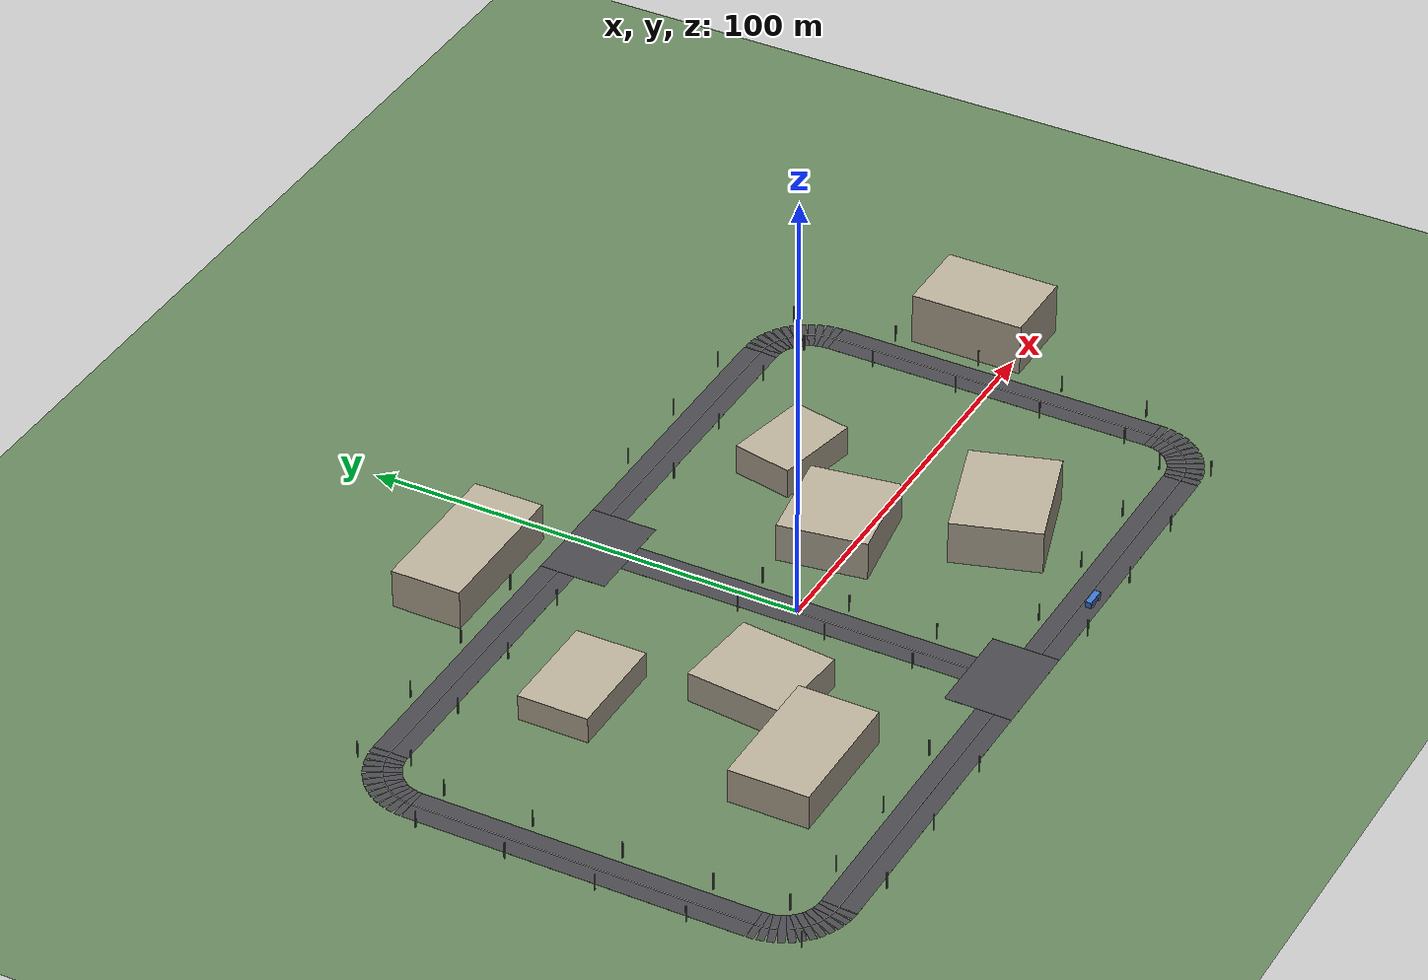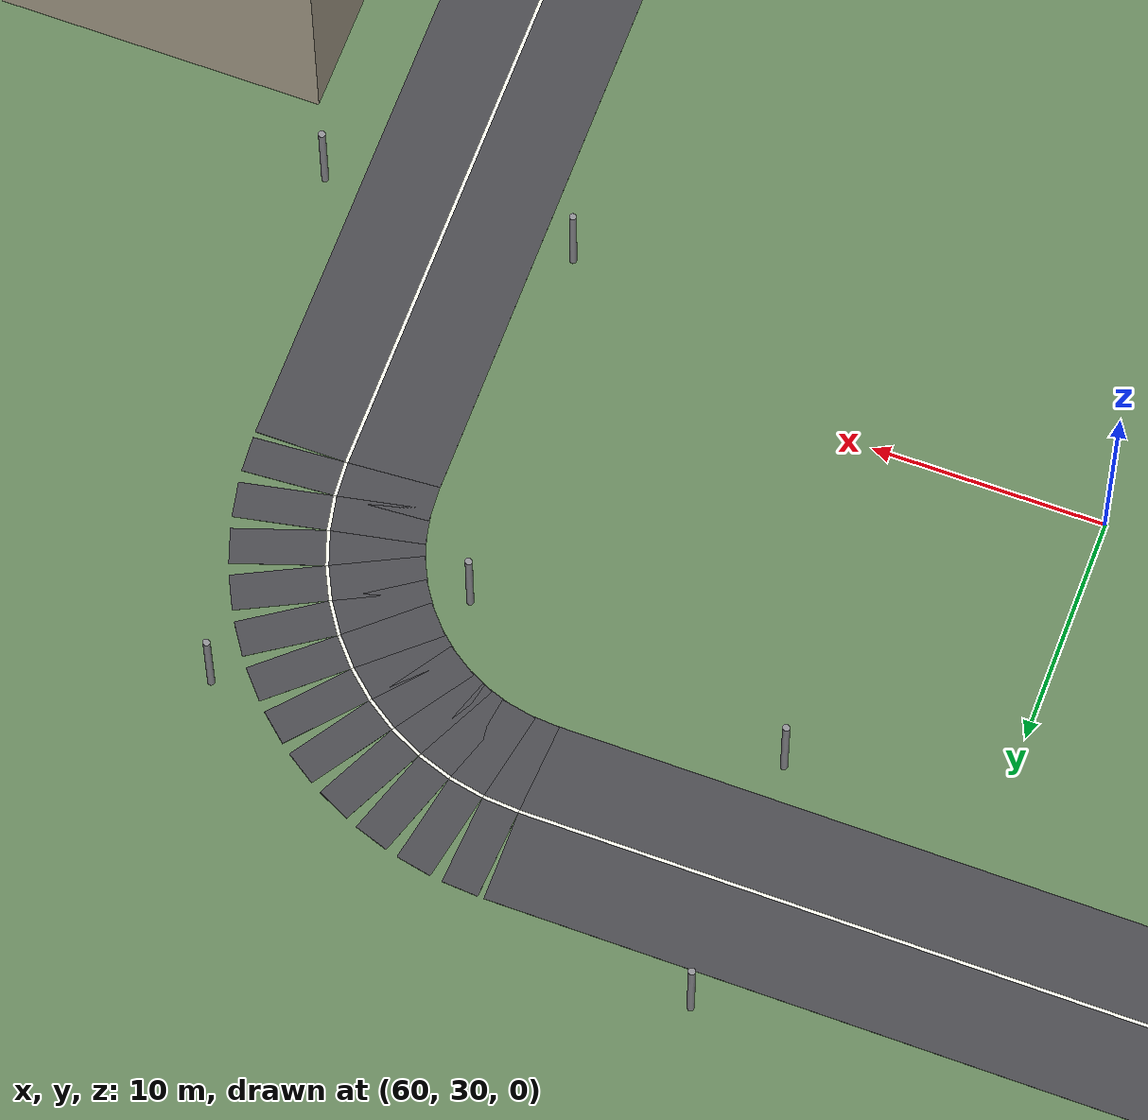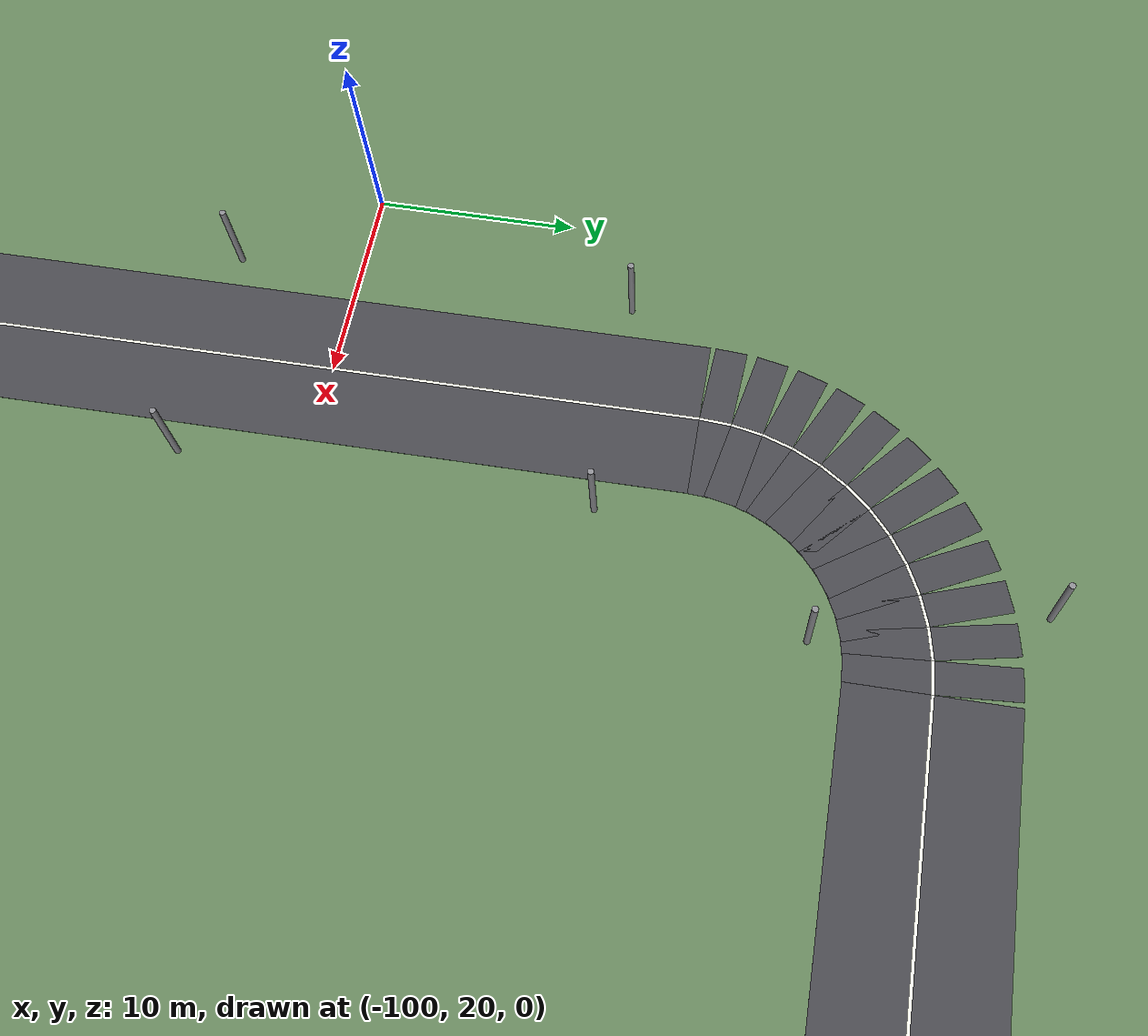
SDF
<?xml version="1.0" ?>
<sdf version="1.9">
  <world name="campus_loop">

    <physics name="1ms" type="ignored">
      <max_step_size>0.001</max_step_size>
      <real_time_factor>1.0</real_time_factor>
    </physics>

    <spherical_coordinates>
      <surface_model>EARTH_WGS84</surface_model>
      <world_frame_orientation>ENU</world_frame_orientation>
      <latitude_deg>31.230416</latitude_deg>
      <longitude_deg>121.473701</longitude_deg>
      <elevation>10.0</elevation>
      <heading_deg>0.0</heading_deg>
    </spherical_coordinates>

    <plugin filename="gz-sim-physics-system"
            name="gz::sim::systems::Physics"/>
    <plugin filename="gz-sim-user-commands-system"
            name="gz::sim::systems::UserCommands"/>
    <plugin filename="gz-sim-scene-broadcaster-system"
            name="gz::sim::systems::SceneBroadcaster"/>
    <plugin filename="gz-sim-sensors-system"
            name="gz::sim::systems::Sensors">
      <render_engine>ogre2</render_engine>
    </plugin>
    <plugin filename="gz-sim-imu-system"
            name="gz::sim::systems::Imu"/>
    <plugin filename="gz-sim-navsat-system"
            name="gz::sim::systems::NavSat"/>

    <scene>
      <ambient>0.6 0.6 0.6 1</ambient>
      <background>0.75 0.82 0.9 1</background>
      <!-- 关阴影。ODD 限定白天晴朗（SPEC §2），阴影对算法毫无价值，
           但它是 RTF 的头号消耗项之一。地图变大后这一条更要紧。 -->
      <shadows>false</shadows>
    </scene>

    <light type="directional" name="sun">
      <cast_shadows>false</cast_shadows>
      <pose>0 0 10 0 0 0</pose>
      <diffuse>0.9 0.9 0.9 1</diffuse>
      <specular>0.2 0.2 0.2 1</specular>
      <direction>-0.4 0.3 -0.9</direction>
    </light>

    <!-- 地面。环线包络 180×100 m，加上路面宽度约到 ±94 × ±54，
         取 260×180 留出余量，让视野边缘不是一条突兀的截断线。 -->
    <model name="ground_plane">
      <static>true</static>
      <link name="link">
        <collision name="collision">
          <geometry><plane><normal>0 0 1</normal><size>260 180</size></plane></geometry>
          <surface>
            <friction><ode><mu>1.0</mu><mu2>1.0</mu2></ode></friction>
          </surface>
        </collision>
        <visual name="visual">
          <geometry><plane><normal>0 0 1</normal><size>260 180</size></plane></geometry>
          <material>
            <ambient>0.35 0.45 0.32 1</ambient>
            <diffuse>0.4 0.52 0.36 1</diffuse>
          </material>
        </visual>
      </link>
    </model>

    <include>
      <uri>model://campus_road</uri>
      <name>campus_road</name>
      <pose>0 0 0 0 0 0</pose>
    </include>

    <include>
      <uri>model://campus_structures</uri>
      <name>campus_structures</name>
      <pose>0 0 0 0 0 0</pose>
    </include>

    <include>
      <uri>model://ego_vehicle</uri>
      <name>ego_vehicle</name>
      <pose>30 -51.75 0 0 0 0</pose>
    </include>

  </world>
</sdf>

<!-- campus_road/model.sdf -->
<sdf version="1.9">
  <model name="campus_road">
    <static>true</static>
    <link name="link">
      <visual name="surface_0">
        <pose>44.500000 -50.000000 0.005000 0 0 0.000000</pose>
        <geometry><box><size>67.000000 8.000000 0.010000</size></box></geometry>
        <material><ambient>0.22 0.22 0.24 1</ambient><diffuse>0.28 0.28 0.30 1</diffuse></material>
      </visual>
      <visual name="centerline_0">
        <pose>44.500000 -50.000000 0.006000 0 0 0.000000</pose>
        <geometry><box><size>67.000000 0.150000 0.010000</size></box></geometry>
        <material><ambient>0.85 0.85 0.80 1</ambient><diffuse>0.95 0.95 0.90 1</diffuse></material>
      </visual>
      <visual name="surface_1">
        <pose>78.783157 -49.948669 0.005000 0 0 0.065450</pose>
        <geometry><box><size>1.569675 8.000000 0.010000</size></box></geometry>
        <material><ambient>0.22 0.22 0.24 1</ambient><diffuse>0.28 0.28 0.30 1</diffuse></material>
      </visual>
      <visual name="centerline_1">
        <pose>78.783157 -49.948669 0.006000 0 0 0.065450</pose>
        <geometry><box><size>1.569675 0.150000 0.010000</size></box></geometry>
        <material><ambient>0.85 0.85 0.80 1</ambient><diffuse>0.95 0.95 0.90 1</diffuse></material>
      </visual>
      <visual name="surface_2">
        <pose>80.336071 -49.744224 0.005000 0 0 0.196350</pose>
        <geometry><box><size>1.569675 8.000000 0.010000</size></box></geometry>
        <material><ambient>0.22 0.22 0.24 1</ambient><diffuse>0.28 0.28 0.30 1</diffuse></material>
      </visual>
      <visual name="centerline_2">
        <pose>80.336071 -49.744224 0.006000 0 0 0.196350</pose>
        <geometry><box><size>1.569675 0.150000 0.010000</size></box></geometry>
        <material><ambient>0.85 0.85 0.80 1</ambient><diffuse>0.95 0.95 0.90 1</diffuse></material>
      </visual>
      <visual name="surface_3">
        <pose>81.849015 -49.338832 0.005000 0 0 0.327249</pose>
        <geometry><box><size>1.569675 8.000000 0.010000</size></box></geometry>
        <material><ambient>0.22 0.22 0.24 1</ambient><diffuse>0.28 0.28 0.30 1</diffuse></material>
      </visual>
      <visual name="centerline_3">
        <pose>81.849015 -49.338832 0.006000 0 0 0.327249</pose>
        <geometry><box><size>1.569675 0.150000 0.010000</size></box></geometry>
        <material><ambient>0.85 0.85 0.80 1</ambient><diffuse>0.95 0.95 0.90 1</diffuse></material>
      </visual>
      <visual name="surface_4">
        <pose>83.296101 -48.739430 0.005000 0 0 0.458149</pose>
        <geometry><box><size>1.569675 8.000000 0.010000</size></box></geometry>
        <material><ambient>0.22 0.22 0.24 1</ambient><diffuse>0.28 0.28 0.30 1</diffuse></material>
      </visual>
      <visual name="centerline_4">
        <pose>83.296101 -48.739430 0.006000 0 0 0.458149</pose>
        <geometry><box><size>1.569675 0.150000 0.010000</size></box></geometry>
        <material><ambient>0.85 0.85 0.80 1</ambient><diffuse>0.95 0.95 0.90 1</diffuse></material>
      </visual>
      <visual name="surface_5">
        <pose>84.652569 -47.956272 0.005000 0 0 0.589049</pose>
        <geometry><box><size>1.569675 8.000000 0.010000</size></box></geometry>
        <material><ambient>0.22 0.22 0.24 1</ambient><diffuse>0.28 0.28 0.30 1</diffuse></material>
      </visual>
      <visual name="centerline_5">
        <pose>84.652569 -47.956272 0.006000 0 0 0.589049</pose>
        <geometry><box><size>1.569675 0.150000 0.010000</size></box></geometry>
        <material><ambient>0.85 0.85 0.80 1</ambient><diffuse>0.95 0.95 0.90 1</diffuse></material>
      </visual>
      <visual name="surface_6">
        <pose>85.895209 -47.002761 0.005000 0 0 0.719948</pose>
        <geometry><box><size>1.569675 8.000000 0.010000</size></box></geometry>
        <material><ambient>0.22 0.22 0.24 1</ambient><diffuse>0.28 0.28 0.30 1</diffuse></material>
      </visual>
      <visual name="centerline_6">
        <pose>85.895209 -47.002761 0.006000 0 0 0.719948</pose>
        <geometry><box><size>1.569675 0.150000 0.010000</size></box></geometry>
        <material><ambient>0.85 0.85 0.80 1</ambient><diffuse>0.95 0.95 0.90 1</diffuse></material>
      </visual>
      <visual name="surface_7">
        <pose>87.002761 -45.895209 0.005000 0 0 0.850848</pose>
        <geometry><box><size>1.569675 8.000000 0.010000</size></box></geometry>
        <material><ambient>0.22 0.22 0.24 1</ambient><diffuse>0.28 0.28 0.30 1</diffuse></material>
      </visual>
      <visual name="centerline_7">
        <pose>87.002761 -45.895209 0.006000 0 0 0.850848</pose>
        <geometry><box><size>1.569675 0.150000 0.010000</size></box></geometry>
        <material><ambient>0.85 0.85 0.80 1</ambient><diffuse>0.95 0.95 0.90 1</diffuse></material>
      </visual>
      <visual name="surface_8">
        <pose>87.956272 -44.652569 0.005000 0 0 0.981748</pose>
        <geometry><box><size>1.569675 8.000000 0.010000</size></box></geometry>
        <material><ambient>0.22 0.22 0.24 1</ambient><diffuse>0.28 0.28 0.30 1</diffuse></material>
      </visual>
      <visual name="centerline_8">
        <pose>87.956272 -44.652569 0.006000 0 0 0.981748</pose>
        <geometry><box><size>1.569675 0.150000 0.010000</size></box></geometry>
        <material><ambient>0.85 0.85 0.80 1</ambient><diffuse>0.95 0.95 0.90 1</diffuse></material>
      </visual>
      <visual name="surface_9">
        <pose>88.739430 -43.296101 0.005000 0 0 1.112647</pose>
        <geometry><box><size>1.569675 8.000000 0.010000</size></box></geometry>
        <material><ambient>0.22 0.22 0.24 1</ambient><diffuse>0.28 0.28 0.30 1</diffuse></material>
      </visual>
      <visual name="centerline_9">
        <pose>88.739430 -43.296101 0.006000 0 0 1.112647</pose>
        <geometry><box><size>1.569675 0.150000 0.010000</size></box></geometry>
        <material><ambient>0.85 0.85 0.80 1</ambient><diffuse>0.95 0.95 0.90 1</diffuse></material>
      </visual>
      <visual name="surface_10">
        <pose>89.338832 -41.849015 0.005000 0 0 1.243547</pose>
        <geometry><box><size>1.569675 8.000000 0.010000</size></box></geometry>
        <material><ambient>0.22 0.22 0.24 1</ambient><diffuse>0.28 0.28 0.30 1</diffuse></material>
      </visual>
      <visual name="centerline_10">
        <pose>89.338832 -41.849015 0.006000 0 0 1.243547</pose>
        <geometry><box><size>1.569675 0.150000 0.010000</size></box></geometry>
        <material><ambient>0.85 0.85 0.80 1</ambient><diffuse>0.95 0.95 0.90 1</diffuse></material>
      </visual>
      <visual name="surface_11">
        <pose>89.744224 -40.336071 0.005000 0 0 1.374447</pose>
        <geometry><box><size>1.569675 8.000000 0.010000</size></box></geometry>
        <material><ambient>0.22 0.22 0.24 1</ambient><diffuse>0.28 0.28 0.30 1</diffuse></material>
      </visual>
      <visual name="centerline_11">
        <pose>89.744224 -40.336071 0.006000 0 0 1.374447</pose>
        <geometry><box><size>1.569675 0.150000 0.010000</size></box></geometry>
        <material><ambient>0.85 0.85 0.80 1</ambient><diffuse>0.95 0.95 0.90 1</diffuse></material>
      </visual>
      <visual name="surface_12">
        <pose>89.948669 -38.783157 0.005000 0 0 1.505346</pose>
        <geometry><box><size>1.569675 8.000000 0.010000</size></box></geometry>
        <material><ambient>0.22 0.22 0.24 1</ambient><diffuse>0.28 0.28 0.30 1</diffuse></material>
      </visual>
      <visual name="centerline_12">
        <pose>89.948669 -38.783157 0.006000 0 0 1.505346</pose>
        <geometry><box><size>1.569675 0.150000 0.010000</size></box></geometry>
        <material><ambient>0.85 0.85 0.80 1</ambient><diffuse>0.95 0.95 0.90 1</diffuse></material>
      </visual>
      <visual name="surface_13">
        <pose>90.000000 0.000000 0.005000 0 0 1.570796</pose>
        <geometry><box><size>76.000000 8.000000 0.010000</size></box></geometry>
        <material><ambient>0.22 0.22 0.24 1</ambient><diffuse>0.28 0.28 0.30 1</diffuse></material>
      </visual>
      <visual name="centerline_13">
        <pose>90.000000 0.000000 0.006000 0 0 1.570796</pose>
        <geometry><box><size>76.000000 0.150000 0.010000</size></box></geometry>
        <material><ambient>0.85 0.85 0.80 1</ambient><diffuse>0.95 0.95 0.90 1</diffuse></material>
      </visual>
      <visual name="surface_14">
        <pose>89.948669 38.783157 0.005000 0 0 1.636246</pose>
        <geometry><box><size>1.569675 8.000000 0.010000</size></box></geometry>
        <material><ambient>0.22 0.22 0.24 1</ambient><diffuse>0.28 0.28 0.30 1</diffuse></material>
      </visual>
      <visual name="centerline_14">
        <pose>89.948669 38.783157 0.006000 0 0 1.636246</pose>
        <geometry><box><size>1.569675 0.150000 0.010000</size></box></geometry>
        <material><ambient>0.85 0.85 0.80 1</ambient><diffuse>0.95 0.95 0.90 1</diffuse></material>
      </visual>
      <visual name="surface_15">
        <pose>89.744224 40.336071 0.005000 0 0 1.767146</pose>
        <geometry><box><size>1.569675 8.000000 0.010000</size></box></geometry>
        <material><ambient>0.22 0.22 0.24 1</ambient><diffuse>0.28 0.28 0.30 1</diffuse></material>
      </visual>
      <visual name="centerline_15">
        <pose>89.744224 40.336071 0.006000 0 0 1.767146</pose>
        <geometry><box><size>1.569675 0.150000 0.010000</size></box></geometry>
        <material><ambient>0.85 0.85 0.80 1</ambient><diffuse>0.95 0.95 0.90 1</diffuse></material>
      </visual>
      <visual name="surface_16">
        <pose>89.338832 41.849015 0.005000 0 0 1.898046</pose>
        <geometry><box><size>1.569675 8.000000 0.010000</size></box></geometry>
        <material><ambient>0.22 0.22 0.24 1</ambient><diffuse>0.28 0.28 0.30 1</diffuse></material>
      </visual>
      <visual name="centerline_16">
        <pose>89.338832 41.849015 0.006000 0 0 1.898046</pose>
        <geometry><box><size>1.569675 0.150000 0.010000</size></box></geometry>
        <material><ambient>0.85 0.85 0.80 1</ambient><diffuse>0.95 0.95 0.90 1</diffuse></material>
      </visual>
      <visual name="surface_17">
        <pose>88.739430 43.296101 0.005000 0 0 2.028945</pose>
        <geometry><box><size>1.569675 8.000000 0.010000</size></box></geometry>
        <material><ambient>0.22 0.22 0.24 1</ambient><diffuse>0.28 0.28 0.30 1</diffuse></material>
      </visual>
      <visual name="centerline_17">
        <pose>88.739430 43.296101 0.006000 0 0 2.028945</pose>
        <geometry><box><size>1.569675 0.150000 0.010000</size></box></geometry>
        <material><ambient>0.85 0.85 0.80 1</ambient><diffuse>0.95 0.95 0.90 1</diffuse></material>
      </visual>
      <visual name="surface_18">
        <pose>87.956272 44.652569 0.005000 0 0 2.159845</pose>
        <geometry><box><size>1.569675 8.000000 0.010000</size></box></geometry>
        <material><ambient>0.22 0.22 0.24 1</ambient><diffuse>0.28 0.28 0.30 1</diffuse></material>
      </visual>
      <visual name="centerline_18">
        <pose>87.956272 44.652569 0.006000 0 0 2.159845</pose>
        <geometry><box><size>1.569675 0.150000 0.010000</size></box></geometry>
        <material><ambient>0.85 0.85 0.80 1</ambient><diffuse>0.95 0.95 0.90 1</diffuse></material>
      </visual>
      <visual name="surface_19">
        <pose>87.002761 45.895209 0.005000 0 0 2.290745</pose>
        <geometry><box><size>1.569675 8.000000 0.010000</size></box></geometry>
        <material><ambient>0.22 0.22 0.24 1</ambient><diffuse>0.28 0.28 0.30 1</diffuse></material>
      </visual>
      <visual name="centerline_19">
        <pose>87.002761 45.895209 0.006000 0 0 2.290745</pose>
        <geometry><box><size>1.569675 0.150000 0.010000</size></box></geometry>
        <material><ambient>0.85 0.85 0.80 1</ambient><diffuse>0.95 0.95 0.90 1</diffuse></material>
      </visual>
      <visual name="surface_20">
        <pose>85.895209 47.002761 0.005000 0 0 2.421644</pose>
        <geometry><box><size>1.569675 8.000000 0.010000</size></box></geometry>
        <material><ambient>0.22 0.22 0.24 1</ambient><diffuse>0.28 0.28 0.30 1</diffuse></material>
      </visual>
      <visual name="centerline_20">
        <pose>85.895209 47.002761 0.006000 0 0 2.421644</pose>
        <geometry><box><size>1.569675 0.150000 0.010000</size></box></geometry>
        <material><ambient>0.85 0.85 0.80 1</ambient><diffuse>0.95 0.95 0.90 1</diffuse></material>
      </visual>
      <visual name="surface_21">
        <pose>84.652569 47.956272 0.005000 0 0 2.552544</pose>
        <geometry><box><size>1.569675 8.000000 0.010000</size></box></geometry>
        <material><ambient>0.22 0.22 0.24 1</ambient><diffuse>0.28 0.28 0.30 1</diffuse></material>
      </visual>
      <visual name="centerline_21">
        <pose>84.652569 47.956272 0.006000 0 0 2.552544</pose>
        <geometry><box><size>1.569675 0.150000 0.010000</size></box></geometry>
        <material><ambient>0.85 0.85 0.80 1</ambient><diffuse>0.95 0.95 0.90 1</diffuse></material>
      </visual>
      <visual name="surface_22">
        <pose>83.296101 48.739430 0.005000 0 0 2.683444</pose>
        <geometry><box><size>1.569675 8.000000 0.010000</size></box></geometry>
        <material><ambient>0.22 0.22 0.24 1</ambient><diffuse>0.28 0.28 0.30 1</diffuse></material>
      </visual>
      <visual name="centerline_22">
        <pose>83.296101 48.739430 0.006000 0 0 2.683444</pose>
        <geometry><box><size>1.569675 0.150000 0.010000</size></box></geometry>
        <material><ambient>0.85 0.85 0.80 1</ambient><diffuse>0.95 0.95 0.90 1</diffuse></material>
      </visual>
      <visual name="surface_23">
        <pose>81.849015 49.338832 0.005000 0 0 2.814343</pose>
        <geometry><box><size>1.569675 8.000000 0.010000</size></box></geometry>
        <material><ambient>0.22 0.22 0.24 1</ambient><diffuse>0.28 0.28 0.30 1</diffuse></material>
      </visual>
      <visual name="centerline_23">
        <pose>81.849015 49.338832 0.006000 0 0 2.814343</pose>
        <geometry><box><size>1.569675 0.150000 0.010000</size></box></geometry>
        <material><ambient>0.85 0.85 0.80 1</ambient><diffuse>0.95 0.95 0.90 1</diffuse></material>
      </visual>
      <visual name="surface_24">
        <pose>80.336071 49.744224 0.005000 0 0 2.945243</pose>
        <geometry><box><size>1.569675 8.000000 0.010000</size></box></geometry>
        <material><ambient>0.22 0.22 0.24 1</ambient><diffuse>0.28 0.28 0.30 1</diffuse></material>
      </visual>
      <visual name="centerline_24">
        <pose>80.336071 49.744224 0.006000 0 0 2.945243</pose>
        <geometry><box><size>1.569675 0.150000 0.010000</size></box></geometry>
        <material><ambient>0.85 0.85 0.80 1</ambient><diffuse>0.95 0.95 0.90 1</diffuse></material>
      </visual>
      <visual name="surface_25">
        <pose>78.783157 49.948669 0.005000 0 0 3.076143</pose>
        <geometry><box><size>1.569675 8.000000 0.010000</size></box></geometry>
        <material><ambient>0.22 0.22 0.24 1</ambient><diffuse>0.28 0.28 0.30 1</diffuse></material>
      </visual>
      <visual name="centerline_25">
        <pose>78.783157 49.948669 0.006000 0 0 3.076143</pose>
        <geometry><box><size>1.569675 0.150000 0.010000</size></box></geometry>
        <material><ambient>0.85 0.85 0.80 1</ambient><diffuse>0.95 0.95 0.90 1</diffuse></material>
      </visual>
      <visual name="surface_26">
        <pose>44.500000 50.000000 0.005000 0 0 3.141593</pose>
        <geometry><box><size>67.000000 8.000000 0.010000</size></box></geometry>
        <material><ambient>0.22 0.22 0.24 1</ambient><diffuse>0.28 0.28 0.30 1</diffuse></material>
      </visual>
      <visual name="centerline_26">
        <pose>44.500000 50.000000 0.006000 0 0 3.141593</pose>
        <geometry><box><size>67.000000 0.150000 0.010000</size></box></geometry>
        <material><ambient>0.85 0.85 0.80 1</ambient><diffuse>0.95 0.95 0.90 1</diffuse></material>
      </visual>
      <visual name="surface_27">
        <pose>-44.500000 50.000000 0.005000 0 0 3.141593</pose>
        <geometry><box><size>67.000000 8.000000 0.010000</size></box></geometry>
        <material><ambient>0.22 0.22 0.24 1</ambient><diffuse>0.28 0.28 0.30 1</diffuse></material>
      </visual>
      <visual name="centerline_27">
        <pose>-44.500000 50.000000 0.006000 0 0 3.141593</pose>
        <geometry><box><size>67.000000 0.150000 0.010000</size></box></geometry>
        <material><ambient>0.85 0.85 0.80 1</ambient><diffuse>0.95 0.95 0.90 1</diffuse></material>
      </visual>
      <visual name="surface_28">
        <pose>-78.783157 49.948669 0.005000 0 0 -3.076143</pose>
        <geometry><box><size>1.569675 8.000000 0.010000</size></box></geometry>
        <material><ambient>0.22 0.22 0.24 1</ambient><diffuse>0.28 0.28 0.30 1</diffuse></material>
      </visual>
      <visual name="centerline_28">
        <pose>-78.783157 49.948669 0.006000 0 0 -3.076143</pose>
        <geometry><box><size>1.569675 0.150000 0.010000</size></box></geometry>
        <material><ambient>0.85 0.85 0.80 1</ambient><diffuse>0.95 0.95 0.90 1</diffuse></material>
      </visual>
      <visual name="surface_29">
        <pose>-80.336071 49.744224 0.005000 0 0 -2.945243</pose>
        <geometry><box><size>1.569675 8.000000 0.010000</size></box></geometry>
        <material><ambient>0.22 0.22 0.24 1</ambient><diffuse>0.28 0.28 0.30 1</diffuse></material>
      </visual>
      <visual name="centerline_29">
        <pose>-80.336071 49.744224 0.006000 0 0 -2.945243</pose>
        <geometry><box><size>1.569675 0.150000 0.010000</size></box></geometry>
        <material><ambient>0.85 0.85 0.80 1</ambient><diffuse>0.95 0.95 0.90 1</diffuse></material>
      </visual>
      <visual name="surface_30">
        <pose>-81.849015 49.338832 0.005000 0 0 -2.814343</pose>
        <geometry><box><size>1.569675 8.000000 0.010000</size></box></geometry>
        <material><ambient>0.22 0.22 0.24 1</ambient><diffuse>0.28 0.28 0.30 1</diffuse></material>
      </visual>
      <visual name="centerline_30">
        <pose>-81.849015 49.338832 0.006000 0 0 -2.814343</pose>
        <geometry><box><size>1.569675 0.150000 0.010000</size></box></geometry>
        <material><ambient>0.85 0.85 0.80 1</ambient><diffuse>0.95 0.95 0.90 1</diffuse></material>
      </visual>
      <visual name="surface_31">
        <pose>-83.296101 48.739430 0.005000 0 0 -2.683444</pose>
        <geometry><box><size>1.569675 8.000000 0.010000</size></box></geometry>
        <material><ambient>0.22 0.22 0.24 1</ambient><diffuse>0.28 0.28 0.30 1</diffuse></material>
      </visual>
      <visual name="centerline_31">
        <pose>-83.296101 48.739430 0.006000 0 0 -2.683444</pose>
        <geometry><box><size>1.569675 0.150000 0.010000</size></box></geometry>
        <material><ambient>0.85 0.85 0.80 1</ambient><diffuse>0.95 0.95 0.90 1</diffuse></material>
      </visual>
      <visual name="surface_32">
        <pose>-84.652569 47.956272 0.005000 0 0 -2.552544</pose>
        <geometry><box><size>1.569675 8.000000 0.010000</size></box></geometry>
        <material><ambient>0.22 0.22 0.24 1</ambient><diffuse>0.28 0.28 0.30 1</diffuse></material>
      </visual>
      <visual name="centerline_32">
        <pose>-84.652569 47.956272 0.006000 0 0 -2.552544</pose>
        <geometry><box><size>1.569675 0.150000 0.010000</size></box></geometry>
        <material><ambient>0.85 0.85 0.80 1</ambient><diffuse>0.95 0.95 0.90 1</diffuse></material>
      </visual>
      <visual name="surface_33">
        <pose>-85.895209 47.002761 0.005000 0 0 -2.421644</pose>
        <geometry><box><size>1.569675 8.000000 0.010000</size></box></geometry>
        <material><ambient>0.22 0.22 0.24 1</ambient><diffuse>0.28 0.28 0.30 1</diffuse></material>
      </visual>
      <visual name="centerline_33">
        <pose>-85.895209 47.002761 0.006000 0 0 -2.421644</pose>
        <geometry><box><size>1.569675 0.150000 0.010000</size></box></geometry>
        <material><ambient>0.85 0.85 0.80 1</ambient><diffuse>0.95 0.95 0.90 1</diffuse></material>
      </visual>
      <visual name="surface_34">
        <pose>-87.002761 45.895209 0.005000 0 0 -2.290745</pose>
        <geometry><box><size>1.569675 8.000000 0.010000</size></box></geometry>
        <material><ambient>0.22 0.22 0.24 1</ambient><diffuse>0.28 0.28 0.30 1</diffuse></material>
      </visual>
      <visual name="centerline_34">
        <pose>-87.002761 45.895209 0.006000 0 0 -2.290745</pose>
        <geometry><box><size>1.569675 0.150000 0.010000</size></box></geometry>
        <material><ambient>0.85 0.85 0.80 1</ambient><diffuse>0.95 0.95 0.90 1</diffuse></material>
      </visual>
      <visual name="surface_35">
        <pose>-87.956272 44.652569 0.005000 0 0 -2.159845</pose>
        <geometry><box><size>1.569675 8.000000 0.010000</size></box></geometry>
        <material><ambient>0.22 0.22 0.24 1</ambient><diffuse>0.28 0.28 0.30 1</diffuse></material>
      </visual>
      <visual name="centerline_35">
        <pose>-87.956272 44.652569 0.006000 0 0 -2.159845</pose>
        <geometry><box><size>1.569675 0.150000 0.010000</size></box></geometry>
        <material><ambient>0.85 0.85 0.80 1</ambient><diffuse>0.95 0.95 0.90 1</diffuse></material>
      </visual>
      <visual name="surface_36">
        <pose>-88.739430 43.296101 0.005000 0 0 -2.028945</pose>
        <geometry><box><size>1.569675 8.000000 0.010000</size></box></geometry>
        <material><ambient>0.22 0.22 0.24 1</ambient><diffuse>0.28 0.28 0.30 1</diffuse></material>
      </visual>
      <visual name="centerline_36">
        <pose>-88.739430 43.296101 0.006000 0 0 -2.028945</pose>
        <geometry><box><size>1.569675 0.150000 0.010000</size></box></geometry>
        <material><ambient>0.85 0.85 0.80 1</ambient><diffuse>0.95 0.95 0.90 1</diffuse></material>
      </visual>
      <visual name="surface_37">
        <pose>-89.338832 41.849015 0.005000 0 0 -1.898046</pose>
        <geometry><box><size>1.569675 8.000000 0.010000</size></box></geometry>
        <material><ambient>0.22 0.22 0.24 1</ambient><diffuse>0.28 0.28 0.30 1</diffuse></material>
      </visual>
      <visual name="centerline_37">
        <pose>-89.338832 41.849015 0.006000 0 0 -1.898046</pose>
        <geometry><box><size>1.569675 0.150000 0.010000</size></box></geometry>
        <material><ambient>0.85 0.85 0.80 1</ambient><diffuse>0.95 0.95 0.90 1</diffuse></material>
      </visual>
      <visual name="surface_38">
        <pose>-89.744224 40.336071 0.005000 0 0 -1.767146</pose>
        <geometry><box><size>1.569675 8.000000 0.010000</size></box></geometry>
        <material><ambient>0.22 0.22 0.24 1</ambient><diffuse>0.28 0.28 0.30 1</diffuse></material>
      </visual>
      <visual name="centerline_38">
        <pose>-89.744224 40.336071 0.006000 0 0 -1.767146</pose>
        <geometry><box><size>1.569675 0.150000 0.010000</size></box></geometry>
        <material><ambient>0.85 0.85 0.80 1</ambient><diffuse>0.95 0.95 0.90 1</diffuse></material>
      </visual>
      <visual name="surface_39">
        <pose>-89.948669 38.783157 0.005000 0 0 -1.636246</pose>
        <geometry><box><size>1.569675 8.000000 0.010000</size></box></geometry>
        <material><ambient>0.22 0.22 0.24 1</ambient><diffuse>0.28 0.28 0.30 1</diffuse></material>
      </visual>
      <visual name="centerline_39">
        <pose>-89.948669 38.783157 0.006000 0 0 -1.636246</pose>
        <geometry><box><size>1.569675 0.150000 0.010000</size></box></geometry>
        <material><ambient>0.85 0.85 0.80 1</ambient><diffuse>0.95 0.95 0.90 1</diffuse></material>
      </visual>
      <visual name="surface_40">
        <pose>-90.000000 0.000000 0.005000 0 0 -1.570796</pose>
        <geometry><box><size>76.000000 8.000000 0.010000</size></box></geometry>
        <material><ambient>0.22 0.22 0.24 1</ambient><diffuse>0.28 0.28 0.30 1</diffuse></material>
      </visual>
      <visual name="centerline_40">
        <pose>-90.000000 0.000000 0.006000 0 0 -1.570796</pose>
        <geometry><box><size>76.000000 0.150000 0.010000</size></box></geometry>
        <material><ambient>0.85 0.85 0.80 1</ambient><diffuse>0.95 0.95 0.90 1</diffuse></material>
      </visual>
      <visual name="surface_41">
        <pose>-89.948669 -38.783157 0.005000 0 0 -1.505346</pose>
        <geometry><box><size>1.569675 8.000000 0.010000</size></box></geometry>
        <material><ambient>0.22 0.22 0.24 1</ambient><diffuse>0.28 0.28 0.30 1</diffuse></material>
      </visual>
      <visual name="centerline_41">
        <pose>-89.948669 -38.783157 0.006000 0 0 -1.505346</pose>
        <geometry><box><size>1.569675 0.150000 0.010000</size></box></geometry>
        <material><ambient>0.85 0.85 0.80 1</ambient><diffuse>0.95 0.95 0.90 1</diffuse></material>
      </visual>
      <visual name="surface_42">
        <pose>-89.744224 -40.336071 0.005000 0 0 -1.374447</pose>
        <geometry><box><size>1.569675 8.000000 0.010000</size></box></geometry>
        <material><ambient>0.22 0.22 0.24 1</ambient><diffuse>0.28 0.28 0.30 1</diffuse></material>
      </visual>
      <visual name="centerline_42">
        <pose>-89.744224 -40.336071 0.006000 0 0 -1.374447</pose>
        <geometry><box><size>1.569675 0.150000 0.010000</size></box></geometry>
        <material><ambient>0.85 0.85 0.80 1</ambient><diffuse>0.95 0.95 0.90 1</diffuse></material>
      </visual>
      <visual name="surface_43">
        <pose>-89.338832 -41.849015 0.005000 0 0 -1.243547</pose>
        <geometry><box><size>1.569675 8.000000 0.010000</size></box></geometry>
        <material><ambient>0.22 0.22 0.24 1</ambient><diffuse>0.28 0.28 0.30 1</diffuse></material>
      </visual>
      <visual name="centerline_43">
        <pose>-89.338832 -41.849015 0.006000 0 0 -1.243547</pose>
        <geometry><box><size>1.569675 0.150000 0.010000</size></box></geometry>
        <material><ambient>0.85 0.85 0.80 1</ambient><diffuse>0.95 0.95 0.90 1</diffuse></material>
      </visual>
      <visual name="surface_44">
        <pose>-88.739430 -43.296101 0.005000 0 0 -1.112647</pose>
        <geometry><box><size>1.569675 8.000000 0.010000</size></box></geometry>
        <material><ambient>0.22 0.22 0.24 1</ambient><diffuse>0.28 0.28 0.30 1</diffuse></material>
      </visual>
      <visual name="centerline_44">
        <pose>-88.739430 -43.296101 0.006000 0 0 -1.112647</pose>
        <geometry><box><size>1.569675 0.150000 0.010000</size></box></geometry>
        <material><ambient>0.85 0.85 0.80 1</ambient><diffuse>0.95 0.95 0.90 1</diffuse></material>
      </visual>
      <visual name="surface_45">
        <pose>-87.956272 -44.652569 0.005000 0 0 -0.981748</pose>
        <geometry><box><size>1.569675 8.000000 0.010000</size></box></geometry>
        <material><ambient>0.22 0.22 0.24 1</ambient><diffuse>0.28 0.28 0.30 1</diffuse></material>
      </visual>
      <visual name="centerline_45">
        <pose>-87.956272 -44.652569 0.006000 0 0 -0.981748</pose>
        <geometry><box><size>1.569675 0.150000 0.010000</size></box></geometry>
        <material><ambient>0.85 0.85 0.80 1</ambient><diffuse>0.95 0.95 0.90 1</diffuse></material>
      </visual>
      <visual name="surface_46">
        <pose>-87.002761 -45.895209 0.005000 0 0 -0.850848</pose>
        <geometry><box><size>1.569675 8.000000 0.010000</size></box></geometry>
        <material><ambient>0.22 0.22 0.24 1</ambient><diffuse>0.28 0.28 0.30 1</diffuse></material>
      </visual>
      <visual name="centerline_46">
        <pose>-87.002761 -45.895209 0.006000 0 0 -0.850848</pose>
        <geometry><box><size>1.569675 0.150000 0.010000</size></box></geometry>
        <material><ambient>0.85 0.85 0.80 1</ambient><diffuse>0.95 0.95 0.90 1</diffuse></material>
      </visual>
      <visual name="surface_47">
        <pose>-85.895209 -47.002761 0.005000 0 0 -0.719948</pose>
        <geometry><box><size>1.569675 8.000000 0.010000</size></box></geometry>
        <material><ambient>0.22 0.22 0.24 1</ambient><diffuse>0.28 0.28 0.30 1</diffuse></material>
      </visual>
      <visual name="centerline_47">
        <pose>-85.895209 -47.002761 0.006000 0 0 -0.719948</pose>
        <geometry><box><size>1.569675 0.150000 0.010000</size></box></geometry>
        <material><ambient>0.85 0.85 0.80 1</ambient><diffuse>0.95 0.95 0.90 1</diffuse></material>
      </visual>
      <visual name="surface_48">
        <pose>-84.652569 -47.956272 0.005000 0 0 -0.589049</pose>
        <geometry><box><size>1.569675 8.000000 0.010000</size></box></geometry>
        <material><ambient>0.22 0.22 0.24 1</ambient><diffuse>0.28 0.28 0.30 1</diffuse></material>
      </visual>
      <visual name="centerline_48">
        <pose>-84.652569 -47.956272 0.006000 0 0 -0.589049</pose>
        <geometry><box><size>1.569675 0.150000 0.010000</size></box></geometry>
        <material><ambient>0.85 0.85 0.80 1</ambient><diffuse>0.95 0.95 0.90 1</diffuse></material>
      </visual>
      <visual name="surface_49">
        <pose>-83.296101 -48.739430 0.005000 0 0 -0.458149</pose>
        <geometry><box><size>1.569675 8.000000 0.010000</size></box></geometry>
        <material><ambient>0.22 0.22 0.24 1</ambient><diffuse>0.28 0.28 0.30 1</diffuse></material>
      </visual>
      <visual name="centerline_49">
        <pose>-83.296101 -48.739430 0.006000 0 0 -0.458149</pose>
        <geometry><box><size>1.569675 0.150000 0.010000</size></box></geometry>
        <material><ambient>0.85 0.85 0.80 1</ambient><diffuse>0.95 0.95 0.90 1</diffuse></material>
      </visual>
      <visual name="surface_50">
        <pose>-81.849015 -49.338832 0.005000 0 0 -0.327249</pose>
        <geometry><box><size>1.569675 8.000000 0.010000</size></box></geometry>
        <material><ambient>0.22 0.22 0.24 1</ambient><diffuse>0.28 0.28 0.30 1</diffuse></material>
      </visual>
      <visual name="centerline_50">
        <pose>-81.849015 -49.338832 0.006000 0 0 -0.327249</pose>
        <geometry><box><size>1.569675 0.150000 0.010000</size></box></geometry>
        <material><ambient>0.85 0.85 0.80 1</ambient><diffuse>0.95 0.95 0.90 1</diffuse></material>
      </visual>
      <visual name="surface_51">
        <pose>-80.336071 -49.744224 0.005000 0 0 -0.196350</pose>
        <geometry><box><size>1.569675 8.000000 0.010000</size></box></geometry>
        <material><ambient>0.22 0.22 0.24 1</ambient><diffuse>0.28 0.28 0.30 1</diffuse></material>
      </visual>
      <visual name="centerline_51">
        <pose>-80.336071 -49.744224 0.006000 0 0 -0.196350</pose>
        <geometry><box><size>1.569675 0.150000 0.010000</size></box></geometry>
        <material><ambient>0.85 0.85 0.80 1</ambient><diffuse>0.95 0.95 0.90 1</diffuse></material>
      </visual>
      <visual name="surface_52">
        <pose>-78.783157 -49.948669 0.005000 0 0 -0.065450</pose>
        <geometry><box><size>1.569675 8.000000 0.010000</size></box></geometry>
        <material><ambient>0.22 0.22 0.24 1</ambient><diffuse>0.28 0.28 0.30 1</diffuse></material>
      </visual>
      <visual name="centerline_52">
        <pose>-78.783157 -49.948669 0.006000 0 0 -0.065450</pose>
        <geometry><box><size>1.569675 0.150000 0.010000</size></box></geometry>
        <material><ambient>0.85 0.85 0.80 1</ambient><diffuse>0.95 0.95 0.90 1</diffuse></material>
      </visual>
      <visual name="surface_53">
        <pose>-44.500000 -50.000000 0.005000 0 0 0.000000</pose>
        <geometry><box><size>67.000000 8.000000 0.010000</size></box></geometry>
        <material><ambient>0.22 0.22 0.24 1</ambient><diffuse>0.28 0.28 0.30 1</diffuse></material>
      </visual>
      <visual name="centerline_53">
        <pose>-44.500000 -50.000000 0.006000 0 0 0.000000</pose>
        <geometry><box><size>67.000000 0.150000 0.010000</size></box></geometry>
        <material><ambient>0.85 0.85 0.80 1</ambient><diffuse>0.95 0.95 0.90 1</diffuse></material>
      </visual>
      <visual name="surface_54">
        <pose>0.000000 0.000000 0.005000 0 0 1.570796</pose>
        <geometry><box><size>78.000000 8.000000 0.010000</size></box></geometry>
        <material><ambient>0.22 0.22 0.24 1</ambient><diffuse>0.28 0.28 0.30 1</diffuse></material>
      </visual>
      <visual name="centerline_54">
        <pose>0.000000 0.000000 0.006000 0 0 1.570796</pose>
        <geometry><box><size>78.000000 0.150000 0.010000</size></box></geometry>
        <material><ambient>0.85 0.85 0.80 1</ambient><diffuse>0.95 0.95 0.90 1</diffuse></material>
      </visual>
      <visual name="junction_100">
        <pose>0.000000 -46.500000 0.005000 0 0 0.000000</pose>
        <geometry><box><size>22.000000 15.000000 0.010000</size></box></geometry>
        <material><ambient>0.22 0.22 0.24 1</ambient><diffuse>0.28 0.28 0.30 1</diffuse></material>
      </visual>
      <visual name="junction_101">
        <pose>0.000000 46.500000 0.005000 0 0 0.000000</pose>
        <geometry><box><size>22.000000 15.000000 0.010000</size></box></geometry>
        <material><ambient>0.22 0.22 0.24 1</ambient><diffuse>0.28 0.28 0.30 1</diffuse></material>
      </visual>
    </link>
  </model>
</sdf>

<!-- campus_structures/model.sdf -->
<sdf version="1.9">
  <model name="campus_structures">
    <static>true</static>
    <link name="link">
      <visual name="pole_loop_east_0l_visual">
        <pose>21.000000 -44.500000 2.000000 0 0 0</pose>
        <geometry><cylinder><radius>0.150000</radius><length>4.000000</length></cylinder></geometry>
        <material><ambient>0.45 0.45 0.47 1</ambient><diffuse>0.55 0.55 0.57 1</diffuse></material>
      </visual>
      <collision name="pole_loop_east_0l_collision">
        <pose>21.000000 -44.500000 2.000000 0 0 0</pose>
        <geometry><cylinder><radius>0.150000</radius><length>4.000000</length></cylinder></geometry>
      </collision>
      <visual name="pole_loop_east_0r_visual">
        <pose>21.000000 -55.500000 2.000000 0 0 0</pose>
        <geometry><cylinder><radius>0.150000</radius><length>4.000000</length></cylinder></geometry>
        <material><ambient>0.45 0.45 0.47 1</ambient><diffuse>0.55 0.55 0.57 1</diffuse></material>
      </visual>
      <collision name="pole_loop_east_0r_collision">
        <pose>21.000000 -55.500000 2.000000 0 0 0</pose>
        <geometry><cylinder><radius>0.150000</radius><length>4.000000</length></cylinder></geometry>
      </collision>
      <visual name="pole_loop_east_1l_visual">
        <pose>41.000000 -44.500000 2.000000 0 0 0</pose>
        <geometry><cylinder><radius>0.150000</radius><length>4.000000</length></cylinder></geometry>
        <material><ambient>0.45 0.45 0.47 1</ambient><diffuse>0.55 0.55 0.57 1</diffuse></material>
      </visual>
      <collision name="pole_loop_east_1l_collision">
        <pose>41.000000 -44.500000 2.000000 0 0 0</pose>
        <geometry><cylinder><radius>0.150000</radius><length>4.000000</length></cylinder></geometry>
      </collision>
      <visual name="pole_loop_east_1r_visual">
        <pose>41.000000 -55.500000 2.000000 0 0 0</pose>
        <geometry><cylinder><radius>0.150000</radius><length>4.000000</length></cylinder></geometry>
        <material><ambient>0.45 0.45 0.47 1</ambient><diffuse>0.55 0.55 0.57 1</diffuse></material>
      </visual>
      <collision name="pole_loop_east_1r_collision">
        <pose>41.000000 -55.500000 2.000000 0 0 0</pose>
        <geometry><cylinder><radius>0.150000</radius><length>4.000000</length></cylinder></geometry>
      </collision>
      <visual name="pole_loop_east_2l_visual">
        <pose>61.000000 -44.500000 2.000000 0 0 0</pose>
        <geometry><cylinder><radius>0.150000</radius><length>4.000000</length></cylinder></geometry>
        <material><ambient>0.45 0.45 0.47 1</ambient><diffuse>0.55 0.55 0.57 1</diffuse></material>
      </visual>
      <collision name="pole_loop_east_2l_collision">
        <pose>61.000000 -44.500000 2.000000 0 0 0</pose>
        <geometry><cylinder><radius>0.150000</radius><length>4.000000</length></cylinder></geometry>
      </collision>
      <visual name="pole_loop_east_2r_visual">
        <pose>61.000000 -55.500000 2.000000 0 0 0</pose>
        <geometry><cylinder><radius>0.150000</radius><length>4.000000</length></cylinder></geometry>
        <material><ambient>0.45 0.45 0.47 1</ambient><diffuse>0.55 0.55 0.57 1</diffuse></material>
      </visual>
      <collision name="pole_loop_east_2r_collision">
        <pose>61.000000 -55.500000 2.000000 0 0 0</pose>
        <geometry><cylinder><radius>0.150000</radius><length>4.000000</length></cylinder></geometry>
      </collision>
      <visual name="pole_loop_east_3l_visual">
        <pose>79.608126 -44.297931 2.000000 0 0 0</pose>
        <geometry><cylinder><radius>0.150000</radius><length>4.000000</length></cylinder></geometry>
        <material><ambient>0.45 0.45 0.47 1</ambient><diffuse>0.55 0.55 0.57 1</diffuse></material>
      </visual>
      <collision name="pole_loop_east_3l_collision">
        <pose>79.608126 -44.297931 2.000000 0 0 0</pose>
        <geometry><cylinder><radius>0.150000</radius><length>4.000000</length></cylinder></geometry>
      </collision>
      <visual name="pole_loop_east_3r_visual">
        <pose>82.329569 -54.955967 2.000000 0 0 0</pose>
        <geometry><cylinder><radius>0.150000</radius><length>4.000000</length></cylinder></geometry>
        <material><ambient>0.45 0.45 0.47 1</ambient><diffuse>0.55 0.55 0.57 1</diffuse></material>
      </visual>
      <collision name="pole_loop_east_3r_collision">
        <pose>82.329569 -54.955967 2.000000 0 0 0</pose>
        <geometry><cylinder><radius>0.150000</radius><length>4.000000</length></cylinder></geometry>
      </collision>
      <visual name="pole_loop_east_4l_visual">
        <pose>84.500000 -33.849556 2.000000 0 0 0</pose>
        <geometry><cylinder><radius>0.150000</radius><length>4.000000</length></cylinder></geometry>
        <material><ambient>0.45 0.45 0.47 1</ambient><diffuse>0.55 0.55 0.57 1</diffuse></material>
      </visual>
      <collision name="pole_loop_east_4l_collision">
        <pose>84.500000 -33.849556 2.000000 0 0 0</pose>
        <geometry><cylinder><radius>0.150000</radius><length>4.000000</length></cylinder></geometry>
      </collision>
      <visual name="pole_loop_east_4r_visual">
        <pose>95.500000 -33.849556 2.000000 0 0 0</pose>
        <geometry><cylinder><radius>0.150000</radius><length>4.000000</length></cylinder></geometry>
        <material><ambient>0.45 0.45 0.47 1</ambient><diffuse>0.55 0.55 0.57 1</diffuse></material>
      </visual>
      <collision name="pole_loop_east_4r_collision">
        <pose>95.500000 -33.849556 2.000000 0 0 0</pose>
        <geometry><cylinder><radius>0.150000</radius><length>4.000000</length></cylinder></geometry>
      </collision>
      <visual name="pole_loop_east_5l_visual">
        <pose>84.500000 -13.849556 2.000000 0 0 0</pose>
        <geometry><cylinder><radius>0.150000</radius><length>4.000000</length></cylinder></geometry>
        <material><ambient>0.45 0.45 0.47 1</ambient><diffuse>0.55 0.55 0.57 1</diffuse></material>
      </visual>
      <collision name="pole_loop_east_5l_collision">
        <pose>84.500000 -13.849556 2.000000 0 0 0</pose>
        <geometry><cylinder><radius>0.150000</radius><length>4.000000</length></cylinder></geometry>
      </collision>
      <visual name="pole_loop_east_5r_visual">
        <pose>95.500000 -13.849556 2.000000 0 0 0</pose>
        <geometry><cylinder><radius>0.150000</radius><length>4.000000</length></cylinder></geometry>
        <material><ambient>0.45 0.45 0.47 1</ambient><diffuse>0.55 0.55 0.57 1</diffuse></material>
      </visual>
      <collision name="pole_loop_east_5r_collision">
        <pose>95.500000 -13.849556 2.000000 0 0 0</pose>
        <geometry><cylinder><radius>0.150000</radius><length>4.000000</length></cylinder></geometry>
      </collision>
      <visual name="pole_loop_east_6l_visual">
        <pose>84.500000 6.150444 2.000000 0 0 0</pose>
        <geometry><cylinder><radius>0.150000</radius><length>4.000000</length></cylinder></geometry>
        <material><ambient>0.45 0.45 0.47 1</ambient><diffuse>0.55 0.55 0.57 1</diffuse></material>
      </visual>
      <collision name="pole_loop_east_6l_collision">
        <pose>84.500000 6.150444 2.000000 0 0 0</pose>
        <geometry><cylinder><radius>0.150000</radius><length>4.000000</length></cylinder></geometry>
      </collision>
      <visual name="pole_loop_east_6r_visual">
        <pose>95.500000 6.150444 2.000000 0 0 0</pose>
        <geometry><cylinder><radius>0.150000</radius><length>4.000000</length></cylinder></geometry>
        <material><ambient>0.45 0.45 0.47 1</ambient><diffuse>0.55 0.55 0.57 1</diffuse></material>
      </visual>
      <collision name="pole_loop_east_6r_collision">
        <pose>95.500000 6.150444 2.000000 0 0 0</pose>
        <geometry><cylinder><radius>0.150000</radius><length>4.000000</length></cylinder></geometry>
      </collision>
      <visual name="pole_loop_east_7l_visual">
        <pose>84.500000 26.150444 2.000000 0 0 0</pose>
        <geometry><cylinder><radius>0.150000</radius><length>4.000000</length></cylinder></geometry>
        <material><ambient>0.45 0.45 0.47 1</ambient><diffuse>0.55 0.55 0.57 1</diffuse></material>
      </visual>
      <collision name="pole_loop_east_7l_collision">
        <pose>84.500000 26.150444 2.000000 0 0 0</pose>
        <geometry><cylinder><radius>0.150000</radius><length>4.000000</length></cylinder></geometry>
      </collision>
      <visual name="pole_loop_east_7r_visual">
        <pose>95.500000 26.150444 2.000000 0 0 0</pose>
        <geometry><cylinder><radius>0.150000</radius><length>4.000000</length></cylinder></geometry>
        <material><ambient>0.45 0.45 0.47 1</ambient><diffuse>0.55 0.55 0.57 1</diffuse></material>
      </visual>
      <collision name="pole_loop_east_7r_collision">
        <pose>95.500000 26.150444 2.000000 0 0 0</pose>
        <geometry><cylinder><radius>0.150000</radius><length>4.000000</length></cylinder></geometry>
      </collision>
      <visual name="pole_loop_east_8l_visual">
        <pose>83.057476 42.083129 2.000000 0 0 0</pose>
        <geometry><cylinder><radius>0.150000</radius><length>4.000000</length></cylinder></geometry>
        <material><ambient>0.45 0.45 0.47 1</ambient><diffuse>0.55 0.55 0.57 1</diffuse></material>
      </visual>
      <collision name="pole_loop_east_8l_collision">
        <pose>83.057476 42.083129 2.000000 0 0 0</pose>
        <geometry><cylinder><radius>0.150000</radius><length>4.000000</length></cylinder></geometry>
      </collision>
      <visual name="pole_loop_east_8r_visual">
        <pose>91.616281 48.993038 2.000000 0 0 0</pose>
        <geometry><cylinder><radius>0.150000</radius><length>4.000000</length></cylinder></geometry>
        <material><ambient>0.45 0.45 0.47 1</ambient><diffuse>0.55 0.55 0.57 1</diffuse></material>
      </visual>
      <collision name="pole_loop_east_8r_collision">
        <pose>91.616281 48.993038 2.000000 0 0 0</pose>
        <geometry><cylinder><radius>0.150000</radius><length>4.000000</length></cylinder></geometry>
      </collision>
      <visual name="pole_loop_east_9l_visual">
        <pose>68.699112 44.500000 2.000000 0 0 0</pose>
        <geometry><cylinder><radius>0.150000</radius><length>4.000000</length></cylinder></geometry>
        <material><ambient>0.45 0.45 0.47 1</ambient><diffuse>0.55 0.55 0.57 1</diffuse></material>
      </visual>
      <collision name="pole_loop_east_9l_collision">
        <pose>68.699112 44.500000 2.000000 0 0 0</pose>
        <geometry><cylinder><radius>0.150000</radius><length>4.000000</length></cylinder></geometry>
      </collision>
      <visual name="pole_loop_east_9r_visual">
        <pose>68.699112 55.500000 2.000000 0 0 0</pose>
        <geometry><cylinder><radius>0.150000</radius><length>4.000000</length></cylinder></geometry>
        <material><ambient>0.45 0.45 0.47 1</ambient><diffuse>0.55 0.55 0.57 1</diffuse></material>
      </visual>
      <collision name="pole_loop_east_9r_collision">
        <pose>68.699112 55.500000 2.000000 0 0 0</pose>
        <geometry><cylinder><radius>0.150000</radius><length>4.000000</length></cylinder></geometry>
      </collision>
      <visual name="pole_loop_east_10l_visual">
        <pose>48.699112 44.500000 2.000000 0 0 0</pose>
        <geometry><cylinder><radius>0.150000</radius><length>4.000000</length></cylinder></geometry>
        <material><ambient>0.45 0.45 0.47 1</ambient><diffuse>0.55 0.55 0.57 1</diffuse></material>
      </visual>
      <collision name="pole_loop_east_10l_collision">
        <pose>48.699112 44.500000 2.000000 0 0 0</pose>
        <geometry><cylinder><radius>0.150000</radius><length>4.000000</length></cylinder></geometry>
      </collision>
      <visual name="pole_loop_east_10r_visual">
        <pose>48.699112 55.500000 2.000000 0 0 0</pose>
        <geometry><cylinder><radius>0.150000</radius><length>4.000000</length></cylinder></geometry>
        <material><ambient>0.45 0.45 0.47 1</ambient><diffuse>0.55 0.55 0.57 1</diffuse></material>
      </visual>
      <collision name="pole_loop_east_10r_collision">
        <pose>48.699112 55.500000 2.000000 0 0 0</pose>
        <geometry><cylinder><radius>0.150000</radius><length>4.000000</length></cylinder></geometry>
      </collision>
      <visual name="pole_loop_east_11l_visual">
        <pose>28.699112 44.500000 2.000000 0 0 0</pose>
        <geometry><cylinder><radius>0.150000</radius><length>4.000000</length></cylinder></geometry>
        <material><ambient>0.45 0.45 0.47 1</ambient><diffuse>0.55 0.55 0.57 1</diffuse></material>
      </visual>
      <collision name="pole_loop_east_11l_collision">
        <pose>28.699112 44.500000 2.000000 0 0 0</pose>
        <geometry><cylinder><radius>0.150000</radius><length>4.000000</length></cylinder></geometry>
      </collision>
      <visual name="pole_loop_east_11r_visual">
        <pose>28.699112 55.500000 2.000000 0 0 0</pose>
        <geometry><cylinder><radius>0.150000</radius><length>4.000000</length></cylinder></geometry>
        <material><ambient>0.45 0.45 0.47 1</ambient><diffuse>0.55 0.55 0.57 1</diffuse></material>
      </visual>
      <collision name="pole_loop_east_11r_collision">
        <pose>28.699112 55.500000 2.000000 0 0 0</pose>
        <geometry><cylinder><radius>0.150000</radius><length>4.000000</length></cylinder></geometry>
      </collision>
      <visual name="pole_loop_west_0l_visual">
        <pose>-21.000000 44.500000 2.000000 0 0 0</pose>
        <geometry><cylinder><radius>0.150000</radius><length>4.000000</length></cylinder></geometry>
        <material><ambient>0.45 0.45 0.47 1</ambient><diffuse>0.55 0.55 0.57 1</diffuse></material>
      </visual>
      <collision name="pole_loop_west_0l_collision">
        <pose>-21.000000 44.500000 2.000000 0 0 0</pose>
        <geometry><cylinder><radius>0.150000</radius><length>4.000000</length></cylinder></geometry>
      </collision>
      <visual name="pole_loop_west_0r_visual">
        <pose>-21.000000 55.500000 2.000000 0 0 0</pose>
        <geometry><cylinder><radius>0.150000</radius><length>4.000000</length></cylinder></geometry>
        <material><ambient>0.45 0.45 0.47 1</ambient><diffuse>0.55 0.55 0.57 1</diffuse></material>
      </visual>
      <collision name="pole_loop_west_0r_collision">
        <pose>-21.000000 55.500000 2.000000 0 0 0</pose>
        <geometry><cylinder><radius>0.150000</radius><length>4.000000</length></cylinder></geometry>
      </collision>
      <visual name="pole_loop_west_1l_visual">
        <pose>-41.000000 44.500000 2.000000 0 0 0</pose>
        <geometry><cylinder><radius>0.150000</radius><length>4.000000</length></cylinder></geometry>
        <material><ambient>0.45 0.45 0.47 1</ambient><diffuse>0.55 0.55 0.57 1</diffuse></material>
      </visual>
      <collision name="pole_loop_west_1l_collision">
        <pose>-41.000000 44.500000 2.000000 0 0 0</pose>
        <geometry><cylinder><radius>0.150000</radius><length>4.000000</length></cylinder></geometry>
      </collision>
      <visual name="pole_loop_west_1r_visual">
        <pose>-41.000000 55.500000 2.000000 0 0 0</pose>
        <geometry><cylinder><radius>0.150000</radius><length>4.000000</length></cylinder></geometry>
        <material><ambient>0.45 0.45 0.47 1</ambient><diffuse>0.55 0.55 0.57 1</diffuse></material>
      </visual>
      <collision name="pole_loop_west_1r_collision">
        <pose>-41.000000 55.500000 2.000000 0 0 0</pose>
        <geometry><cylinder><radius>0.150000</radius><length>4.000000</length></cylinder></geometry>
      </collision>
      <visual name="pole_loop_west_2l_visual">
        <pose>-61.000000 44.500000 2.000000 0 0 0</pose>
        <geometry><cylinder><radius>0.150000</radius><length>4.000000</length></cylinder></geometry>
        <material><ambient>0.45 0.45 0.47 1</ambient><diffuse>0.55 0.55 0.57 1</diffuse></material>
      </visual>
      <collision name="pole_loop_west_2l_collision">
        <pose>-61.000000 44.500000 2.000000 0 0 0</pose>
        <geometry><cylinder><radius>0.150000</radius><length>4.000000</length></cylinder></geometry>
      </collision>
      <visual name="pole_loop_west_2r_visual">
        <pose>-61.000000 55.500000 2.000000 0 0 0</pose>
        <geometry><cylinder><radius>0.150000</radius><length>4.000000</length></cylinder></geometry>
        <material><ambient>0.45 0.45 0.47 1</ambient><diffuse>0.55 0.55 0.57 1</diffuse></material>
      </visual>
      <collision name="pole_loop_west_2r_collision">
        <pose>-61.000000 55.500000 2.000000 0 0 0</pose>
        <geometry><cylinder><radius>0.150000</radius><length>4.000000</length></cylinder></geometry>
      </collision>
      <visual name="pole_loop_west_3l_visual">
        <pose>-79.608126 44.297931 2.000000 0 0 0</pose>
        <geometry><cylinder><radius>0.150000</radius><length>4.000000</length></cylinder></geometry>
        <material><ambient>0.45 0.45 0.47 1</ambient><diffuse>0.55 0.55 0.57 1</diffuse></material>
      </visual>
      <collision name="pole_loop_west_3l_collision">
        <pose>-79.608126 44.297931 2.000000 0 0 0</pose>
        <geometry><cylinder><radius>0.150000</radius><length>4.000000</length></cylinder></geometry>
      </collision>
      <visual name="pole_loop_west_3r_visual">
        <pose>-82.329569 54.955967 2.000000 0 0 0</pose>
        <geometry><cylinder><radius>0.150000</radius><length>4.000000</length></cylinder></geometry>
        <material><ambient>0.45 0.45 0.47 1</ambient><diffuse>0.55 0.55 0.57 1</diffuse></material>
      </visual>
      <collision name="pole_loop_west_3r_collision">
        <pose>-82.329569 54.955967 2.000000 0 0 0</pose>
        <geometry><cylinder><radius>0.150000</radius><length>4.000000</length></cylinder></geometry>
      </collision>
      <visual name="pole_loop_west_4l_visual">
        <pose>-84.500000 33.849556 2.000000 0 0 0</pose>
        <geometry><cylinder><radius>0.150000</radius><length>4.000000</length></cylinder></geometry>
        <material><ambient>0.45 0.45 0.47 1</ambient><diffuse>0.55 0.55 0.57 1</diffuse></material>
      </visual>
      <collision name="pole_loop_west_4l_collision">
        <pose>-84.500000 33.849556 2.000000 0 0 0</pose>
        <geometry><cylinder><radius>0.150000</radius><length>4.000000</length></cylinder></geometry>
      </collision>
      <visual name="pole_loop_west_4r_visual">
        <pose>-95.500000 33.849556 2.000000 0 0 0</pose>
        <geometry><cylinder><radius>0.150000</radius><length>4.000000</length></cylinder></geometry>
        <material><ambient>0.45 0.45 0.47 1</ambient><diffuse>0.55 0.55 0.57 1</diffuse></material>
      </visual>
      <collision name="pole_loop_west_4r_collision">
        <pose>-95.500000 33.849556 2.000000 0 0 0</pose>
        <geometry><cylinder><radius>0.150000</radius><length>4.000000</length></cylinder></geometry>
      </collision>
      <visual name="pole_loop_west_5l_visual">
        <pose>-84.500000 13.849556 2.000000 0 0 0</pose>
        <geometry><cylinder><radius>0.150000</radius><length>4.000000</length></cylinder></geometry>
        <material><ambient>0.45 0.45 0.47 1</ambient><diffuse>0.55 0.55 0.57 1</diffuse></material>
      </visual>
      <collision name="pole_loop_west_5l_collision">
        <pose>-84.500000 13.849556 2.000000 0 0 0</pose>
        <geometry><cylinder><radius>0.150000</radius><length>4.000000</length></cylinder></geometry>
      </collision>
      <visual name="pole_loop_west_5r_visual">
        <pose>-95.500000 13.849556 2.000000 0 0 0</pose>
        <geometry><cylinder><radius>0.150000</radius><length>4.000000</length></cylinder></geometry>
        <material><ambient>0.45 0.45 0.47 1</ambient><diffuse>0.55 0.55 0.57 1</diffuse></material>
      </visual>
      <collision name="pole_loop_west_5r_collision">
        <pose>-95.500000 13.849556 2.000000 0 0 0</pose>
        <geometry><cylinder><radius>0.150000</radius><length>4.000000</length></cylinder></geometry>
      </collision>
      <visual name="pole_loop_west_6l_visual">
        <pose>-84.500000 -6.150444 2.000000 0 0 0</pose>
        <geometry><cylinder><radius>0.150000</radius><length>4.000000</length></cylinder></geometry>
        <material><ambient>0.45 0.45 0.47 1</ambient><diffuse>0.55 0.55 0.57 1</diffuse></material>
      </visual>
      <collision name="pole_loop_west_6l_collision">
        <pose>-84.500000 -6.150444 2.000000 0 0 0</pose>
        <geometry><cylinder><radius>0.150000</radius><length>4.000000</length></cylinder></geometry>
      </collision>
      <visual name="pole_loop_west_6r_visual">
        <pose>-95.500000 -6.150444 2.000000 0 0 0</pose>
        <geometry><cylinder><radius>0.150000</radius><length>4.000000</length></cylinder></geometry>
        <material><ambient>0.45 0.45 0.47 1</ambient><diffuse>0.55 0.55 0.57 1</diffuse></material>
      </visual>
      <collision name="pole_loop_west_6r_collision">
        <pose>-95.500000 -6.150444 2.000000 0 0 0</pose>
        <geometry><cylinder><radius>0.150000</radius><length>4.000000</length></cylinder></geometry>
      </collision>
      <visual name="pole_loop_west_7l_visual">
        <pose>-84.500000 -26.150444 2.000000 0 0 0</pose>
        <geometry><cylinder><radius>0.150000</radius><length>4.000000</length></cylinder></geometry>
        <material><ambient>0.45 0.45 0.47 1</ambient><diffuse>0.55 0.55 0.57 1</diffuse></material>
      </visual>
      <collision name="pole_loop_west_7l_collision">
        <pose>-84.500000 -26.150444 2.000000 0 0 0</pose>
        <geometry><cylinder><radius>0.150000</radius><length>4.000000</length></cylinder></geometry>
      </collision>
      <visual name="pole_loop_west_7r_visual">
        <pose>-95.500000 -26.150444 2.000000 0 0 0</pose>
        <geometry><cylinder><radius>0.150000</radius><length>4.000000</length></cylinder></geometry>
        <material><ambient>0.45 0.45 0.47 1</ambient><diffuse>0.55 0.55 0.57 1</diffuse></material>
      </visual>
      <collision name="pole_loop_west_7r_collision">
        <pose>-95.500000 -26.150444 2.000000 0 0 0</pose>
        <geometry><cylinder><radius>0.150000</radius><length>4.000000</length></cylinder></geometry>
      </collision>
      <visual name="pole_loop_west_8l_visual">
        <pose>-83.057476 -42.083129 2.000000 0 0 0</pose>
        <geometry><cylinder><radius>0.150000</radius><length>4.000000</length></cylinder></geometry>
        <material><ambient>0.45 0.45 0.47 1</ambient><diffuse>0.55 0.55 0.57 1</diffuse></material>
      </visual>
      <collision name="pole_loop_west_8l_collision">
        <pose>-83.057476 -42.083129 2.000000 0 0 0</pose>
        <geometry><cylinder><radius>0.150000</radius><length>4.000000</length></cylinder></geometry>
      </collision>
      <visual name="pole_loop_west_8r_visual">
        <pose>-91.616281 -48.993038 2.000000 0 0 0</pose>
        <geometry><cylinder><radius>0.150000</radius><length>4.000000</length></cylinder></geometry>
        <material><ambient>0.45 0.45 0.47 1</ambient><diffuse>0.55 0.55 0.57 1</diffuse></material>
      </visual>
      <collision name="pole_loop_west_8r_collision">
        <pose>-91.616281 -48.993038 2.000000 0 0 0</pose>
        <geometry><cylinder><radius>0.150000</radius><length>4.000000</length></cylinder></geometry>
      </collision>
      <visual name="pole_loop_west_9l_visual">
        <pose>-68.699112 -44.500000 2.000000 0 0 0</pose>
        <geometry><cylinder><radius>0.150000</radius><length>4.000000</length></cylinder></geometry>
        <material><ambient>0.45 0.45 0.47 1</ambient><diffuse>0.55 0.55 0.57 1</diffuse></material>
      </visual>
      <collision name="pole_loop_west_9l_collision">
        <pose>-68.699112 -44.500000 2.000000 0 0 0</pose>
        <geometry><cylinder><radius>0.150000</radius><length>4.000000</length></cylinder></geometry>
      </collision>
      <visual name="pole_loop_west_9r_visual">
        <pose>-68.699112 -55.500000 2.000000 0 0 0</pose>
        <geometry><cylinder><radius>0.150000</radius><length>4.000000</length></cylinder></geometry>
        <material><ambient>0.45 0.45 0.47 1</ambient><diffuse>0.55 0.55 0.57 1</diffuse></material>
      </visual>
      <collision name="pole_loop_west_9r_collision">
        <pose>-68.699112 -55.500000 2.000000 0 0 0</pose>
        <geometry><cylinder><radius>0.150000</radius><length>4.000000</length></cylinder></geometry>
      </collision>
      <visual name="pole_loop_west_10l_visual">
        <pose>-48.699112 -44.500000 2.000000 0 0 0</pose>
        <geometry><cylinder><radius>0.150000</radius><length>4.000000</length></cylinder></geometry>
        <material><ambient>0.45 0.45 0.47 1</ambient><diffuse>0.55 0.55 0.57 1</diffuse></material>
      </visual>
      <collision name="pole_loop_west_10l_collision">
        <pose>-48.699112 -44.500000 2.000000 0 0 0</pose>
        <geometry><cylinder><radius>0.150000</radius><length>4.000000</length></cylinder></geometry>
      </collision>
      <visual name="pole_loop_west_10r_visual">
        <pose>-48.699112 -55.500000 2.000000 0 0 0</pose>
        <geometry><cylinder><radius>0.150000</radius><length>4.000000</length></cylinder></geometry>
        <material><ambient>0.45 0.45 0.47 1</ambient><diffuse>0.55 0.55 0.57 1</diffuse></material>
      </visual>
      <collision name="pole_loop_west_10r_collision">
        <pose>-48.699112 -55.500000 2.000000 0 0 0</pose>
        <geometry><cylinder><radius>0.150000</radius><length>4.000000</length></cylinder></geometry>
      </collision>
      <visual name="pole_loop_west_11l_visual">
        <pose>-28.699112 -44.500000 2.000000 0 0 0</pose>
        <geometry><cylinder><radius>0.150000</radius><length>4.000000</length></cylinder></geometry>
        <material><ambient>0.45 0.45 0.47 1</ambient><diffuse>0.55 0.55 0.57 1</diffuse></material>
      </visual>
      <collision name="pole_loop_west_11l_collision">
        <pose>-28.699112 -44.500000 2.000000 0 0 0</pose>
        <geometry><cylinder><radius>0.150000</radius><length>4.000000</length></cylinder></geometry>
      </collision>
      <visual name="pole_loop_west_11r_visual">
        <pose>-28.699112 -55.500000 2.000000 0 0 0</pose>
        <geometry><cylinder><radius>0.150000</radius><length>4.000000</length></cylinder></geometry>
        <material><ambient>0.45 0.45 0.47 1</ambient><diffuse>0.55 0.55 0.57 1</diffuse></material>
      </visual>
      <collision name="pole_loop_west_11r_collision">
        <pose>-28.699112 -55.500000 2.000000 0 0 0</pose>
        <geometry><cylinder><radius>0.150000</radius><length>4.000000</length></cylinder></geometry>
      </collision>
      <visual name="pole_cross_0l_visual">
        <pose>-5.500000 -29.000000 2.000000 0 0 0</pose>
        <geometry><cylinder><radius>0.150000</radius><length>4.000000</length></cylinder></geometry>
        <material><ambient>0.45 0.45 0.47 1</ambient><diffuse>0.55 0.55 0.57 1</diffuse></material>
      </visual>
      <collision name="pole_cross_0l_collision">
        <pose>-5.500000 -29.000000 2.000000 0 0 0</pose>
        <geometry><cylinder><radius>0.150000</radius><length>4.000000</length></cylinder></geometry>
      </collision>
      <visual name="pole_cross_0r_visual">
        <pose>5.500000 -29.000000 2.000000 0 0 0</pose>
        <geometry><cylinder><radius>0.150000</radius><length>4.000000</length></cylinder></geometry>
        <material><ambient>0.45 0.45 0.47 1</ambient><diffuse>0.55 0.55 0.57 1</diffuse></material>
      </visual>
      <collision name="pole_cross_0r_collision">
        <pose>5.500000 -29.000000 2.000000 0 0 0</pose>
        <geometry><cylinder><radius>0.150000</radius><length>4.000000</length></cylinder></geometry>
      </collision>
      <visual name="pole_cross_1l_visual">
        <pose>-5.500000 -9.000000 2.000000 0 0 0</pose>
        <geometry><cylinder><radius>0.150000</radius><length>4.000000</length></cylinder></geometry>
        <material><ambient>0.45 0.45 0.47 1</ambient><diffuse>0.55 0.55 0.57 1</diffuse></material>
      </visual>
      <collision name="pole_cross_1l_collision">
        <pose>-5.500000 -9.000000 2.000000 0 0 0</pose>
        <geometry><cylinder><radius>0.150000</radius><length>4.000000</length></cylinder></geometry>
      </collision>
      <visual name="pole_cross_1r_visual">
        <pose>5.500000 -9.000000 2.000000 0 0 0</pose>
        <geometry><cylinder><radius>0.150000</radius><length>4.000000</length></cylinder></geometry>
        <material><ambient>0.45 0.45 0.47 1</ambient><diffuse>0.55 0.55 0.57 1</diffuse></material>
      </visual>
      <collision name="pole_cross_1r_collision">
        <pose>5.500000 -9.000000 2.000000 0 0 0</pose>
        <geometry><cylinder><radius>0.150000</radius><length>4.000000</length></cylinder></geometry>
      </collision>
      <visual name="pole_cross_2l_visual">
        <pose>-5.500000 11.000000 2.000000 0 0 0</pose>
        <geometry><cylinder><radius>0.150000</radius><length>4.000000</length></cylinder></geometry>
        <material><ambient>0.45 0.45 0.47 1</ambient><diffuse>0.55 0.55 0.57 1</diffuse></material>
      </visual>
      <collision name="pole_cross_2l_collision">
        <pose>-5.500000 11.000000 2.000000 0 0 0</pose>
        <geometry><cylinder><radius>0.150000</radius><length>4.000000</length></cylinder></geometry>
      </collision>
      <visual name="pole_cross_2r_visual">
        <pose>5.500000 11.000000 2.000000 0 0 0</pose>
        <geometry><cylinder><radius>0.150000</radius><length>4.000000</length></cylinder></geometry>
        <material><ambient>0.45 0.45 0.47 1</ambient><diffuse>0.55 0.55 0.57 1</diffuse></material>
      </visual>
      <collision name="pole_cross_2r_collision">
        <pose>5.500000 11.000000 2.000000 0 0 0</pose>
        <geometry><cylinder><radius>0.150000</radius><length>4.000000</length></cylinder></geometry>
      </collision>
      <visual name="b_sw_visual">
        <pose>-45.000000 -25.000000 4.000000 0 0 0.000000</pose>
        <geometry><box><size>30.000000 18.000000 8.000000</size></box></geometry>
        <material><ambient>0.60 0.56 0.50 1</ambient><diffuse>0.72 0.68 0.60 1</diffuse></material>
      </visual>
      <collision name="b_sw_collision">
        <pose>-45.000000 -25.000000 4.000000 0 0 0.000000</pose>
        <geometry><box><size>30.000000 18.000000 8.000000</size></box></geometry>
      </collision>
      <visual name="b_nw_visual">
        <pose>-45.000000 25.000000 3.000000 0 0 0.000000</pose>
        <geometry><box><size>24.000000 16.000000 6.000000</size></box></geometry>
        <material><ambient>0.60 0.56 0.50 1</ambient><diffuse>0.72 0.68 0.60 1</diffuse></material>
      </visual>
      <collision name="b_nw_collision">
        <pose>-45.000000 25.000000 3.000000 0 0 0.000000</pose>
        <geometry><box><size>24.000000 16.000000 6.000000</size></box></geometry>
      </collision>
      <visual name="b_se_visual">
        <pose>45.000000 -25.000000 5.000000 0 0 0.300000</pose>
        <geometry><box><size>26.000000 20.000000 10.000000</size></box></geometry>
        <material><ambient>0.60 0.56 0.50 1</ambient><diffuse>0.72 0.68 0.60 1</diffuse></material>
      </visual>
      <collision name="b_se_collision">
        <pose>45.000000 -25.000000 5.000000 0 0 0.300000</pose>
        <geometry><box><size>26.000000 20.000000 10.000000</size></box></geometry>
      </collision>
      <visual name="b_ne_visual">
        <pose>45.000000 25.000000 3.500000 0 0 -0.200000</pose>
        <geometry><box><size>20.000000 14.000000 7.000000</size></box></geometry>
        <material><ambient>0.60 0.56 0.50 1</ambient><diffuse>0.72 0.68 0.60 1</diffuse></material>
      </visual>
      <collision name="b_ne_collision">
        <pose>45.000000 25.000000 3.500000 0 0 -0.200000</pose>
        <geometry><box><size>20.000000 14.000000 7.000000</size></box></geometry>
      </collision>
      <visual name="b_north_visual">
        <pose>-20.000000 66.000000 4.500000 0 0 0.000000</pose>
        <geometry><box><size>34.000000 16.000000 9.000000</size></box></geometry>
        <material><ambient>0.60 0.56 0.50 1</ambient><diffuse>0.72 0.68 0.60 1</diffuse></material>
      </visual>
      <collision name="b_north_collision">
        <pose>-20.000000 66.000000 4.500000 0 0 0.000000</pose>
        <geometry><box><size>34.000000 16.000000 9.000000</size></box></geometry>
      </collision>
      <visual name="b_east_visual">
        <pose>106.000000 10.000000 6.000000 0 0 0.000000</pose>
        <geometry><box><size>18.000000 26.000000 12.000000</size></box></geometry>
        <material><ambient>0.60 0.56 0.50 1</ambient><diffuse>0.72 0.68 0.60 1</diffuse></material>
      </visual>
      <collision name="b_east_collision">
        <pose>106.000000 10.000000 6.000000 0 0 0.000000</pose>
        <geometry><box><size>18.000000 26.000000 12.000000</size></box></geometry>
      </collision>
      <visual name="b_mid_e_visual">
        <pose>26.000000 4.000000 4.500000 0 0 0.150000</pose>
        <geometry><box><size>22.000000 20.000000 9.000000</size></box></geometry>
        <material><ambient>0.60 0.56 0.50 1</ambient><diffuse>0.72 0.68 0.60 1</diffuse></material>
      </visual>
      <collision name="b_mid_e_collision">
        <pose>26.000000 4.000000 4.500000 0 0 0.150000</pose>
        <geometry><box><size>22.000000 20.000000 9.000000</size></box></geometry>
      </collision>
      <visual name="b_mid_w_visual">
        <pose>-27.000000 -6.000000 3.500000 0 0 -0.100000</pose>
        <geometry><box><size>20.000000 22.000000 7.000000</size></box></geometry>
        <material><ambient>0.60 0.56 0.50 1</ambient><diffuse>0.72 0.68 0.60 1</diffuse></material>
      </visual>
      <collision name="b_mid_w_collision">
        <pose>-27.000000 -6.000000 3.500000 0 0 -0.100000</pose>
        <geometry><box><size>20.000000 22.000000 7.000000</size></box></geometry>
      </collision>
    </link>
  </model>
</sdf>

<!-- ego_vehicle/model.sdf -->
<sdf version="1.9">
  <model name="ego_vehicle">
    <link name="base_link">
      <inertial>
        <!-- 质心不在几何中心：真车质量集中在下半部，用 com_height_m 显式指定。
             放在几何中心会让车过弯时侧倾偏大，看着像悬架太软。 -->
        <pose>1.3500 0 0.5500 0 0 0</pose>
        <mass>1440.0000</mass>
        <inertia>
          <ixx>434.172000</ixx><iyy>2538.672000</iyy><izz>2541.900000</izz>
          <ixy>0</ixy><ixz>0</ixz><iyz>0</iyz>
        </inertia>
      </inertial>
      <collision name="collision">
        <pose>1.3500 0 0.8300 0 0 0</pose>
        <geometry>
          <box><size>4.4000 1.3500 1.3400</size></box>
        </geometry>
      </collision>
      <visual name="visual">
        <pose>1.3500 0 0.8300 0 0 0</pose>
        <geometry>
          <box><size>4.4000 1.3500 1.3400</size></box>
        </geometry>
        <material>
          <ambient>0.2 0.35 0.6 1</ambient>
          <diffuse>0.25 0.45 0.8 1</diffuse>
        </material>
      </visual>

      <sensor name="lidar" type="gpu_lidar">
        <pose>1.3500 0.0000 2.2000 0 0 0</pose>
        <topic>/model/ego_vehicle/lidar</topic>
        <gz_frame_id>lidar_link</gz_frame_id>
        <update_rate>10.0</update_rate>
        <always_on>1</always_on>
        <!-- visualize 只影响 Gazebo GUI 里画不画射线。开着很直观，但几万条
             射线的绘制开销不小，会拉低 RTF —— 调试时临时开，平时关。 -->
        <visualize>false</visualize>
        <lidar>
          <scan>
            <horizontal>
              <samples>1800</samples>
              <resolution>1</resolution>
              <min_angle>-3.141593</min_angle>
              <max_angle>3.141593</max_angle>
            </horizontal>
            <vertical>
              <samples>32</samples>
              <resolution>1</resolution>
              <min_angle>-0.436300</min_angle>
              <max_angle>0.174500</max_angle>
            </vertical>
          </scan>
          <range>
            <min>2.2000</min>
            <max>50.0000</max>
            <!-- 距离量化步长。真实雷达受 ADC 位数限制，这里给 1 cm。 -->
            <resolution>0.01</resolution>
          </range>
          <noise>
            <type>gaussian</type>
            <mean>0.0</mean>
            <stddev>0.0100</stddev>
          </noise>
        </lidar>
      </sensor>

      <sensor name="imu" type="imu">
        <!-- 位姿为全零：IMU 就装在 base_link 原点，见 YAML 里关于杠杆臂的说明。 -->
        <pose>0.0000 0.0000 0.0000 0 0 0</pose>
        <topic>/model/ego_vehicle/imu</topic>
        <gz_frame_id>base_link</gz_frame_id>
        <update_rate>100.0</update_rate>
        <always_on>1</always_on>
        <imu>
          <angular_velocity>
          <x>
            <noise type="gaussian">
              <mean>0.0</mean>
              <stddev>0.00087</stddev>
              <bias_mean>0.0</bias_mean>
              <bias_stddev>0.001</bias_stddev>
              <dynamic_bias_stddev>4.8e-05</dynamic_bias_stddev>
              <dynamic_bias_correlation_time>100</dynamic_bias_correlation_time>
            </noise>
          </x>
          <y>
            <noise type="gaussian">
              <mean>0.0</mean>
              <stddev>0.00087</stddev>
              <bias_mean>0.0</bias_mean>
              <bias_stddev>0.001</bias_stddev>
              <dynamic_bias_stddev>4.8e-05</dynamic_bias_stddev>
              <dynamic_bias_correlation_time>100</dynamic_bias_correlation_time>
            </noise>
          </y>
          <z>
            <noise type="gaussian">
              <mean>0.0</mean>
              <stddev>0.00087</stddev>
              <bias_mean>0.0</bias_mean>
              <bias_stddev>0.001</bias_stddev>
              <dynamic_bias_stddev>4.8e-05</dynamic_bias_stddev>
              <dynamic_bias_correlation_time>100</dynamic_bias_correlation_time>
            </noise>
          </z>
          </angular_velocity>
          <linear_acceleration>
          <x>
            <noise type="gaussian">
              <mean>0.0</mean>
              <stddev>0.01</stddev>
              <bias_mean>0.0</bias_mean>
              <bias_stddev>0.02</bias_stddev>
              <dynamic_bias_stddev>0.0001</dynamic_bias_stddev>
              <dynamic_bias_correlation_time>100</dynamic_bias_correlation_time>
            </noise>
          </x>
          <y>
            <noise type="gaussian">
              <mean>0.0</mean>
              <stddev>0.01</stddev>
              <bias_mean>0.0</bias_mean>
              <bias_stddev>0.02</bias_stddev>
              <dynamic_bias_stddev>0.0001</dynamic_bias_stddev>
              <dynamic_bias_correlation_time>100</dynamic_bias_correlation_time>
            </noise>
          </y>
          <z>
            <noise type="gaussian">
              <mean>0.0</mean>
              <stddev>0.01</stddev>
              <bias_mean>0.0</bias_mean>
              <bias_stddev>0.02</bias_stddev>
              <dynamic_bias_stddev>0.0001</dynamic_bias_stddev>
              <dynamic_bias_correlation_time>100</dynamic_bias_correlation_time>
            </noise>
          </z>
          </linear_acceleration>
        </imu>
      </sensor>

      <sensor name="navsat" type="navsat">
        <pose>0.5000 0.0000 1.6000 0 0 0</pose>
        <topic>/model/ego_vehicle/navsat</topic>
        <gz_frame_id>gnss_link</gz_frame_id>
        <update_rate>10.0</update_rate>
        <always_on>1</always_on>
        <navsat>
          <position_sensing>
            <horizontal>
              <noise type="gaussian">
                <mean>0.0</mean>
                <stddev>1.79662e-05</stddev>
              </noise>
            </horizontal>
            <vertical>
              <noise type="gaussian">
                <mean>0.0</mean>
                <stddev>4</stddev>
              </noise>
            </vertical>
          </position_sensing>
          <velocity_sensing>
            <horizontal>
              <noise type="gaussian">
                <mean>0.0</mean>
                <stddev>0.05</stddev>
              </noise>
            </horizontal>
            <vertical>
              <noise type="gaussian">
                <mean>0.0</mean>
                <stddev>0.1</stddev>
              </noise>
            </vertical>
          </velocity_sensing>
        </navsat>
      </sensor>
    </link>

    <link name="front_left_steer_link">
      <pose>2.7000 0.7750 0.3100 0 0 0</pose>
      <inertial>
        <mass>1.0</mass>
        <inertia>
          <ixx>0.01</ixx><iyy>0.01</iyy><izz>0.01</izz>
          <ixy>0</ixy><ixz>0</ixz><iyz>0</iyz>
        </inertia>
      </inertial>
    </link>

    <link name="front_right_steer_link">
      <pose>2.7000 -0.7750 0.3100 0 0 0</pose>
      <inertial>
        <mass>1.0</mass>
        <inertia>
          <ixx>0.01</ixx><iyy>0.01</iyy><izz>0.01</izz>
          <ixy>0</ixy><ixz>0</ixz><iyz>0</iyz>
        </inertia>
      </inertial>
    </link>

    <link name="front_left_wheel">
      <pose>2.7000 0.7750 0.3100 0 0 0</pose>
      <inertial>
        <mass>15.0000</mass>
        <inertia>
          <ixx>0.410375</ixx><iyy>0.720750</iyy><izz>0.410375</izz>
          <ixy>0</ixy><ixz>0</ixz><iyz>0</iyz>
        </inertia>
      </inertial>
      <collision name="collision">
        <pose>0 0 0 1.5707963 0 0</pose>
        <geometry>
          <cylinder><radius>0.3100</radius><length>0.2000</length></cylinder>
        </geometry>
        <surface>
          <friction>
            <ode><mu>1.2</mu><mu2>1.0</mu2></ode>
          </friction>
        </surface>
      </collision>
      <visual name="visual">
        <pose>0 0 0 1.5707963 0 0</pose>
        <geometry>
          <cylinder><radius>0.3100</radius><length>0.2000</length></cylinder>
        </geometry>
        <material>
          <ambient>0.1 0.1 0.1 1</ambient>
          <diffuse>0.15 0.15 0.15 1</diffuse>
        </material>
      </visual>
    </link>

    <link name="front_right_wheel">
      <pose>2.7000 -0.7750 0.3100 0 0 0</pose>
      <inertial>
        <mass>15.0000</mass>
        <inertia>
          <ixx>0.410375</ixx><iyy>0.720750</iyy><izz>0.410375</izz>
          <ixy>0</ixy><ixz>0</ixz><iyz>0</iyz>
        </inertia>
      </inertial>
      <collision name="collision">
        <pose>0 0 0 1.5707963 0 0</pose>
        <geometry>
          <cylinder><radius>0.3100</radius><length>0.2000</length></cylinder>
        </geometry>
        <surface>
          <friction>
            <ode><mu>1.2</mu><mu2>1.0</mu2></ode>
          </friction>
        </surface>
      </collision>
      <visual name="visual">
        <pose>0 0 0 1.5707963 0 0</pose>
        <geometry>
          <cylinder><radius>0.3100</radius><length>0.2000</length></cylinder>
        </geometry>
        <material>
          <ambient>0.1 0.1 0.1 1</ambient>
          <diffuse>0.15 0.15 0.15 1</diffuse>
        </material>
      </visual>
    </link>

    <link name="rear_left_wheel">
      <pose>0.0000 0.7750 0.3100 0 0 0</pose>
      <inertial>
        <mass>15.0000</mass>
        <inertia>
          <ixx>0.410375</ixx><iyy>0.720750</iyy><izz>0.410375</izz>
          <ixy>0</ixy><ixz>0</ixz><iyz>0</iyz>
        </inertia>
      </inertial>
      <collision name="collision">
        <pose>0 0 0 1.5707963 0 0</pose>
        <geometry>
          <cylinder><radius>0.3100</radius><length>0.2000</length></cylinder>
        </geometry>
        <surface>
          <friction>
            <ode><mu>1.2</mu><mu2>1.0</mu2></ode>
          </friction>
        </surface>
      </collision>
      <visual name="visual">
        <pose>0 0 0 1.5707963 0 0</pose>
        <geometry>
          <cylinder><radius>0.3100</radius><length>0.2000</length></cylinder>
        </geometry>
        <material>
          <ambient>0.1 0.1 0.1 1</ambient>
          <diffuse>0.15 0.15 0.15 1</diffuse>
        </material>
      </visual>
    </link>

    <link name="rear_right_wheel">
      <pose>0.0000 -0.7750 0.3100 0 0 0</pose>
      <inertial>
        <mass>15.0000</mass>
        <inertia>
          <ixx>0.410375</ixx><iyy>0.720750</iyy><izz>0.410375</izz>
          <ixy>0</ixy><ixz>0</ixz><iyz>0</iyz>
        </inertia>
      </inertial>
      <collision name="collision">
        <pose>0 0 0 1.5707963 0 0</pose>
        <geometry>
          <cylinder><radius>0.3100</radius><length>0.2000</length></cylinder>
        </geometry>
        <surface>
          <friction>
            <ode><mu>1.2</mu><mu2>1.0</mu2></ode>
          </friction>
        </surface>
      </collision>
      <visual name="visual">
        <pose>0 0 0 1.5707963 0 0</pose>
        <geometry>
          <cylinder><radius>0.3100</radius><length>0.2000</length></cylinder>
        </geometry>
        <material>
          <ambient>0.1 0.1 0.1 1</ambient>
          <diffuse>0.15 0.15 0.15 1</diffuse>
        </material>
      </visual>
    </link>

    <joint name="front_left_steer_joint" type="revolute">
      <parent>base_link</parent>
      <child>front_left_steer_link</child>
      <axis>
        <xyz>0 0 1</xyz>
        <limit>
          <lower>-0.6000</lower><upper>0.6000</upper>
          <effort>1.0e6</effort>
        </limit>
      </axis>
    </joint>
    <joint name="front_right_steer_joint" type="revolute">
      <parent>base_link</parent>
      <child>front_right_steer_link</child>
      <axis>
        <xyz>0 0 1</xyz>
        <limit>
          <lower>-0.6000</lower><upper>0.6000</upper>
          <effort>1.0e6</effort>
        </limit>
      </axis>
    </joint>

    <!-- 前轮滚动关节挂在转向节下，不是挂在车体上 —— 这样转向和滚动才是两个自由度 -->
    <joint name="front_left_wheel_joint" type="revolute">
      <parent>front_left_steer_link</parent>
      <child>front_left_wheel</child>
      <axis>
        <xyz>0 1 0</xyz>
        <limit><lower>-1e16</lower><upper>1e16</upper></limit>
      </axis>
    </joint>
    <joint name="front_right_wheel_joint" type="revolute">
      <parent>front_right_steer_link</parent>
      <child>front_right_wheel</child>
      <axis>
        <xyz>0 1 0</xyz>
        <limit><lower>-1e16</lower><upper>1e16</upper></limit>
      </axis>
    </joint>

    <!-- 后轮为驱动轮 -->
    <joint name="rear_left_wheel_joint" type="revolute">
      <parent>base_link</parent>
      <child>rear_left_wheel</child>
      <axis>
        <xyz>0 1 0</xyz>
        <limit><lower>-1e16</lower><upper>1e16</upper></limit>
      </axis>
    </joint>
    <joint name="rear_right_wheel_joint" type="revolute">
      <parent>base_link</parent>
      <child>rear_right_wheel</child>
      <axis>
        <xyz>0 1 0</xyz>
        <limit><lower>-1e16</lower><upper>1e16</upper></limit>
      </axis>
    </joint>

    <plugin filename="gz-sim-ackermann-steering-system"
            name="gz::sim::systems::AckermannSteering">
      <left_joint>rear_left_wheel_joint</left_joint>
      <right_joint>rear_right_wheel_joint</right_joint>
      <left_steering_joint>front_left_steer_joint</left_steering_joint>
      <right_steering_joint>front_right_steer_joint</right_steering_joint>
      <kingpin_width>1.5500</kingpin_width>
      <steering_limit>0.6000</steering_limit>
      <steer_p_gain>20.0000</steer_p_gain>
      <wheel_base>2.7000</wheel_base>
      <wheel_separation>1.5500</wheel_separation>
      <wheel_radius>0.3100</wheel_radius>
      <min_velocity>-8.3330</min_velocity>
      <max_velocity>8.3330</max_velocity>
      <min_acceleration>-3.0000</min_acceleration>
      <max_acceleration>1.5000</max_acceleration>
      <topic>/model/ego_vehicle/cmd_vel</topic>
      <odom_topic>/model/ego_vehicle/odometry</odom_topic>
      <tf_topic>/model/ego_vehicle/tf</tf_topic>
      <frame_id>odom</frame_id>
      <child_frame_id>base_link</child_frame_id>
    </plugin>

    <plugin filename="gz-sim-odometry-publisher-system"
            name="gz::sim::systems::OdometryPublisher">
      <odom_frame>map</odom_frame>
      <robot_base_frame>base_link</robot_base_frame>
      <odom_topic>/model/ego_vehicle/pose_gt</odom_topic>
      <tf_topic>/model/ego_vehicle/pose_gt_tf_unused</tf_topic>
      <dimensions>3</dimensions>
      <odom_publish_frequency>50</odom_publish_frequency>
    </plugin>

    <plugin filename="gz-sim-joint-state-publisher-system"
            name="gz::sim::systems::JointStatePublisher">
      <topic>/model/ego_vehicle/joint_state</topic>
    </plugin>
  </model>
</sdf>
